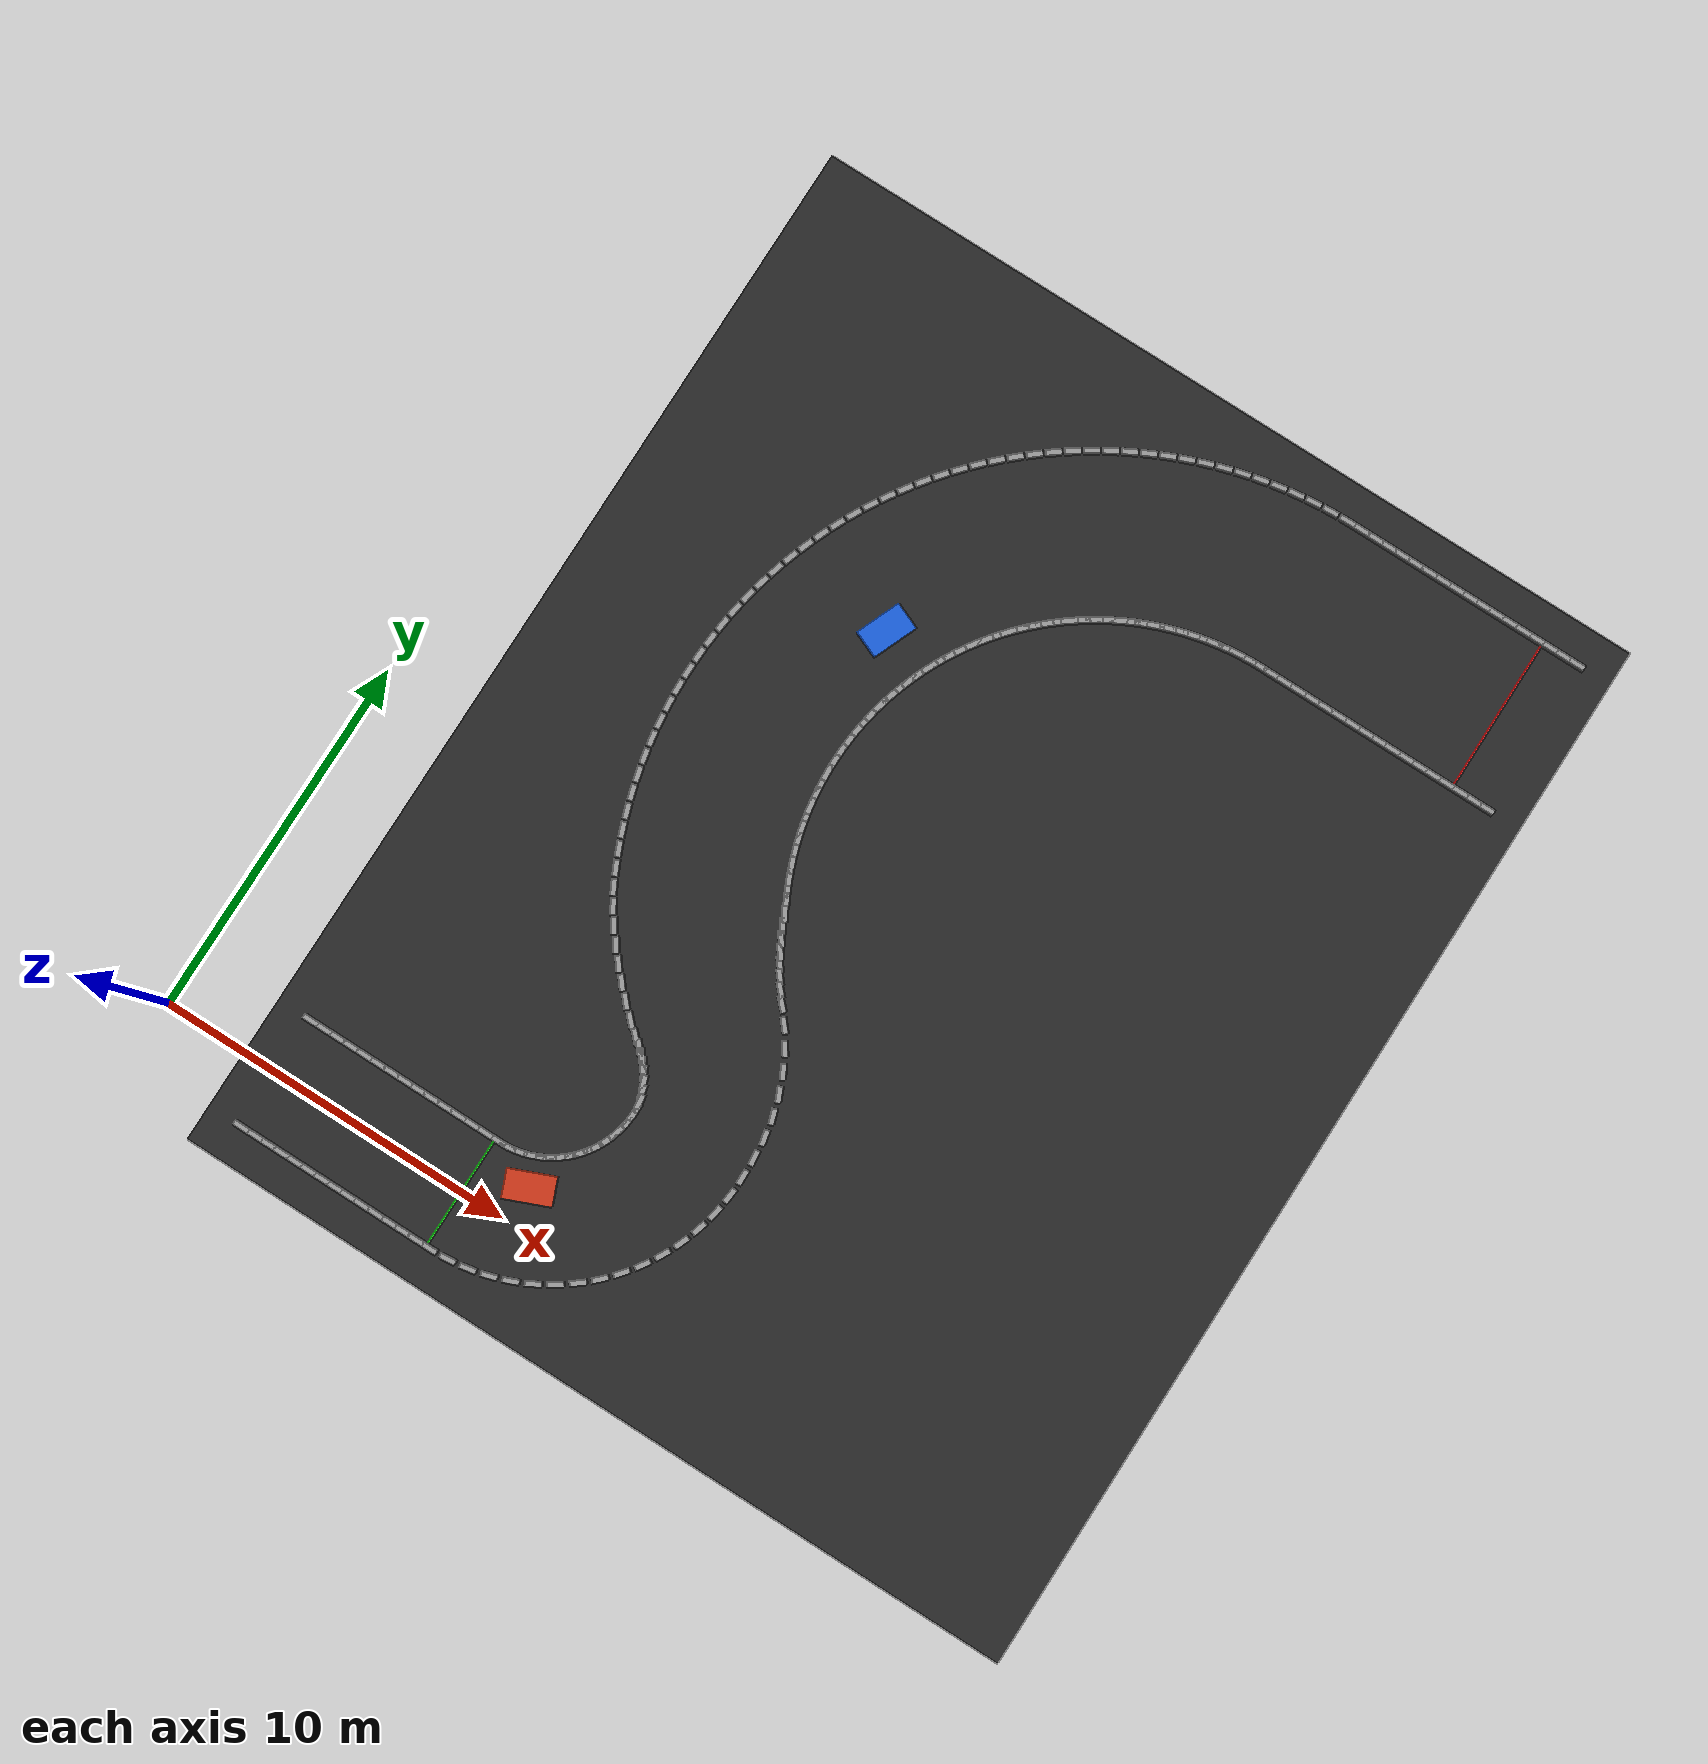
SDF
<?xml version="1.0"?>
<sdf version="1.10">
  <world name="s_curve_avoidance">
    <physics name="default_physics" type="ode">
      <max_step_size>0.001</max_step_size>
      <real_time_factor>1.0</real_time_factor>
    </physics>
    <plugin filename="gz-sim-physics-system" name="gz::sim::systems::Physics"/>
    <plugin filename="gz-sim-user-commands-system" name="gz::sim::systems::UserCommands"/>
    <plugin filename="gz-sim-scene-broadcaster-system" name="gz::sim::systems::SceneBroadcaster"/>
    <plugin filename="gz-sim-sensors-system" name="gz::sim::systems::Sensors">
      <render_engine>ogre2</render_engine>
    </plugin>
    <gravity>0 0 -9.81</gravity>
    <scene>
      <ambient>0.65 0.65 0.65 1</ambient>
      <background>0.78 0.85 0.92 1</background>
      <shadows>true</shadows>
    </scene>
    <light type="directional" name="sun">
      <cast_shadows>true</cast_shadows>
      <pose>20 10 22 0 0 0</pose>
      <diffuse>0.9 0.9 0.9 1</diffuse>
      <specular>0.2 0.2 0.2 1</specular>
      <direction>-0.4 0.1 -0.9</direction>
    </light>

    <model name="s_curve_course">
      <static>true</static>
      <link name="continuous_course">
        <collision name="road_collision">
          <pose>14.245784 12.356933 -0.050000 0 0 0</pose>
          <geometry><box><size>23.991569 29.863866 0.050000</size></box></geometry>
        </collision>
        <visual name="road_visual">
          <pose>14.245784 12.356933 -0.050000 0 0 0</pose>
          <geometry><box><size>23.991569 29.863866 0.050000</size></box></geometry>
          <material><ambient>0.14 0.14 0.14 1</ambient><diffuse>0.16 0.16 0.16 1</diffuse></material>
        </visual>
      </link>
    </model>

    <model name="left_curb_seg_0000">
      <static>true</static>
      <pose>3.250000 1.575000 0.090000 0 0 0.000000</pose>
      <link name="curb">
        <collision name="collision">
          <geometry><box><size>0.432000 0.150000 0.180000</size></box></geometry>
        </collision>
        <visual name="visual">
          <geometry><box><size>0.432000 0.150000 0.180000</size></box></geometry>
          <material><ambient>0.58 0.58 0.58 1</ambient><diffuse>0.62 0.62 0.62 1</diffuse></material>
        </visual>
      </link>
    </model>
    <model name="left_curb_seg_0001">
      <static>true</static>
      <pose>3.650000 1.575000 0.090000 0 0 0.000000</pose>
      <link name="curb">
        <collision name="collision">
          <geometry><box><size>0.432000 0.150000 0.180000</size></box></geometry>
        </collision>
        <visual name="visual">
          <geometry><box><size>0.432000 0.150000 0.180000</size></box></geometry>
          <material><ambient>0.58 0.58 0.58 1</ambient><diffuse>0.62 0.62 0.62 1</diffuse></material>
        </visual>
      </link>
    </model>
    <model name="left_curb_seg_0002">
      <static>true</static>
      <pose>4.050000 1.575000 0.090000 0 0 0.000000</pose>
      <link name="curb">
        <collision name="collision">
          <geometry><box><size>0.432000 0.150000 0.180000</size></box></geometry>
        </collision>
        <visual name="visual">
          <geometry><box><size>0.432000 0.150000 0.180000</size></box></geometry>
          <material><ambient>0.58 0.58 0.58 1</ambient><diffuse>0.62 0.62 0.62 1</diffuse></material>
        </visual>
      </link>
    </model>
    <model name="left_curb_seg_0003">
      <static>true</static>
      <pose>4.450000 1.575000 0.090000 0 0 0.000000</pose>
      <link name="curb">
        <collision name="collision">
          <geometry><box><size>0.432000 0.150000 0.180000</size></box></geometry>
        </collision>
        <visual name="visual">
          <geometry><box><size>0.432000 0.150000 0.180000</size></box></geometry>
          <material><ambient>0.58 0.58 0.58 1</ambient><diffuse>0.62 0.62 0.62 1</diffuse></material>
        </visual>
      </link>
    </model>
    <model name="left_curb_seg_0004">
      <static>true</static>
      <pose>4.850000 1.575000 0.090000 0 0 0.000000</pose>
      <link name="curb">
        <collision name="collision">
          <geometry><box><size>0.432000 0.150000 0.180000</size></box></geometry>
        </collision>
        <visual name="visual">
          <geometry><box><size>0.432000 0.150000 0.180000</size></box></geometry>
          <material><ambient>0.58 0.58 0.58 1</ambient><diffuse>0.62 0.62 0.62 1</diffuse></material>
        </visual>
      </link>
    </model>
    <model name="left_curb_seg_0005">
      <static>true</static>
      <pose>5.250000 1.575000 0.090000 0 0 0.000000</pose>
      <link name="curb">
        <collision name="collision">
          <geometry><box><size>0.432000 0.150000 0.180000</size></box></geometry>
        </collision>
        <visual name="visual">
          <geometry><box><size>0.432000 0.150000 0.180000</size></box></geometry>
          <material><ambient>0.58 0.58 0.58 1</ambient><diffuse>0.62 0.62 0.62 1</diffuse></material>
        </visual>
      </link>
    </model>
    <model name="left_curb_seg_0006">
      <static>true</static>
      <pose>5.650000 1.575000 0.090000 0 0 0.000000</pose>
      <link name="curb">
        <collision name="collision">
          <geometry><box><size>0.432000 0.150000 0.180000</size></box></geometry>
        </collision>
        <visual name="visual">
          <geometry><box><size>0.432000 0.150000 0.180000</size></box></geometry>
          <material><ambient>0.58 0.58 0.58 1</ambient><diffuse>0.62 0.62 0.62 1</diffuse></material>
        </visual>
      </link>
    </model>
    <model name="left_curb_seg_0007">
      <static>true</static>
      <pose>6.050000 1.575000 0.090000 0 0 0.000000</pose>
      <link name="curb">
        <collision name="collision">
          <geometry><box><size>0.432000 0.150000 0.180000</size></box></geometry>
        </collision>
        <visual name="visual">
          <geometry><box><size>0.432000 0.150000 0.180000</size></box></geometry>
          <material><ambient>0.58 0.58 0.58 1</ambient><diffuse>0.62 0.62 0.62 1</diffuse></material>
        </visual>
      </link>
    </model>
    <model name="left_curb_seg_0008">
      <static>true</static>
      <pose>6.450000 1.575000 0.090000 0 0 0.000000</pose>
      <link name="curb">
        <collision name="collision">
          <geometry><box><size>0.432000 0.150000 0.180000</size></box></geometry>
        </collision>
        <visual name="visual">
          <geometry><box><size>0.432000 0.150000 0.180000</size></box></geometry>
          <material><ambient>0.58 0.58 0.58 1</ambient><diffuse>0.62 0.62 0.62 1</diffuse></material>
        </visual>
      </link>
    </model>
    <model name="left_curb_seg_0009">
      <static>true</static>
      <pose>6.850000 1.575000 0.090000 0 0 0.000000</pose>
      <link name="curb">
        <collision name="collision">
          <geometry><box><size>0.432000 0.150000 0.180000</size></box></geometry>
        </collision>
        <visual name="visual">
          <geometry><box><size>0.432000 0.150000 0.180000</size></box></geometry>
          <material><ambient>0.58 0.58 0.58 1</ambient><diffuse>0.62 0.62 0.62 1</diffuse></material>
        </visual>
      </link>
    </model>
    <model name="left_curb_seg_0010">
      <static>true</static>
      <pose>7.250000 1.575000 0.090000 0 0 0.000000</pose>
      <link name="curb">
        <collision name="collision">
          <geometry><box><size>0.432000 0.150000 0.180000</size></box></geometry>
        </collision>
        <visual name="visual">
          <geometry><box><size>0.432000 0.150000 0.180000</size></box></geometry>
          <material><ambient>0.58 0.58 0.58 1</ambient><diffuse>0.62 0.62 0.62 1</diffuse></material>
        </visual>
      </link>
    </model>
    <model name="left_curb_seg_0011">
      <static>true</static>
      <pose>7.650000 1.575000 0.090000 0 0 0.000000</pose>
      <link name="curb">
        <collision name="collision">
          <geometry><box><size>0.432000 0.150000 0.180000</size></box></geometry>
        </collision>
        <visual name="visual">
          <geometry><box><size>0.432000 0.150000 0.180000</size></box></geometry>
          <material><ambient>0.58 0.58 0.58 1</ambient><diffuse>0.62 0.62 0.62 1</diffuse></material>
        </visual>
      </link>
    </model>
    <model name="left_curb_seg_0012">
      <static>true</static>
      <pose>8.050000 1.575000 0.090000 0 0 0.000000</pose>
      <link name="curb">
        <collision name="collision">
          <geometry><box><size>0.432000 0.150000 0.180000</size></box></geometry>
        </collision>
        <visual name="visual">
          <geometry><box><size>0.432000 0.150000 0.180000</size></box></geometry>
          <material><ambient>0.58 0.58 0.58 1</ambient><diffuse>0.62 0.62 0.62 1</diffuse></material>
        </visual>
      </link>
    </model>
    <model name="left_curb_seg_0013">
      <static>true</static>
      <pose>8.450000 1.575000 0.090000 0 0 0.000000</pose>
      <link name="curb">
        <collision name="collision">
          <geometry><box><size>0.432000 0.150000 0.180000</size></box></geometry>
        </collision>
        <visual name="visual">
          <geometry><box><size>0.432000 0.150000 0.180000</size></box></geometry>
          <material><ambient>0.58 0.58 0.58 1</ambient><diffuse>0.62 0.62 0.62 1</diffuse></material>
        </visual>
      </link>
    </model>
    <model name="left_curb_seg_0014">
      <static>true</static>
      <pose>8.843437 1.575126 0.090000 0 0 0.004167</pose>
      <link name="curb">
        <collision name="collision">
          <geometry><box><size>0.432000 0.150000 0.180000</size></box></geometry>
        </collision>
        <visual name="visual">
          <geometry><box><size>0.432000 0.150000 0.180000</size></box></geometry>
          <material><ambient>0.58 0.58 0.58 1</ambient><diffuse>0.62 0.62 0.62 1</diffuse></material>
        </visual>
      </link>
    </model>
    <model name="left_curb_seg_0015">
      <static>true</static>
      <pose>9.111910 1.585217 0.090000 0 0 0.087500</pose>
      <link name="curb">
        <collision name="collision">
          <geometry><box><size>0.432000 0.150000 0.180000</size></box></geometry>
        </collision>
        <visual name="visual">
          <geometry><box><size>0.432000 0.150000 0.180000</size></box></geometry>
          <material><ambient>0.58 0.58 0.58 1</ambient><diffuse>0.62 0.62 0.62 1</diffuse></material>
        </visual>
      </link>
    </model>
    <model name="left_curb_seg_0016">
      <static>true</static>
      <pose>9.352021 1.618442 0.090000 0 0 0.187500</pose>
      <link name="curb">
        <collision name="collision">
          <geometry><box><size>0.432000 0.150000 0.180000</size></box></geometry>
        </collision>
        <visual name="visual">
          <geometry><box><size>0.432000 0.150000 0.180000</size></box></geometry>
          <material><ambient>0.58 0.58 0.58 1</ambient><diffuse>0.62 0.62 0.62 1</diffuse></material>
        </visual>
      </link>
    </model>
    <model name="left_curb_seg_0017">
      <static>true</static>
      <pose>9.587615 1.675472 0.090000 0 0 0.287500</pose>
      <link name="curb">
        <collision name="collision">
          <geometry><box><size>0.432000 0.150000 0.180000</size></box></geometry>
        </collision>
        <visual name="visual">
          <geometry><box><size>0.432000 0.150000 0.180000</size></box></geometry>
          <material><ambient>0.58 0.58 0.58 1</ambient><diffuse>0.62 0.62 0.62 1</diffuse></material>
        </visual>
      </link>
    </model>
    <model name="left_curb_seg_0018">
      <static>true</static>
      <pose>9.816339 1.755737 0.090000 0 0 0.387500</pose>
      <link name="curb">
        <collision name="collision">
          <geometry><box><size>0.432000 0.150000 0.180000</size></box></geometry>
        </collision>
        <visual name="visual">
          <geometry><box><size>0.432000 0.150000 0.180000</size></box></geometry>
          <material><ambient>0.58 0.58 0.58 1</ambient><diffuse>0.62 0.62 0.62 1</diffuse></material>
        </visual>
      </link>
    </model>
    <model name="left_curb_seg_0019">
      <static>true</static>
      <pose>10.035907 1.858436 0.090000 0 0 0.487500</pose>
      <link name="curb">
        <collision name="collision">
          <geometry><box><size>0.432000 0.150000 0.180000</size></box></geometry>
        </collision>
        <visual name="visual">
          <geometry><box><size>0.432000 0.150000 0.180000</size></box></geometry>
          <material><ambient>0.58 0.58 0.58 1</ambient><diffuse>0.62 0.62 0.62 1</diffuse></material>
        </visual>
      </link>
    </model>
    <model name="left_curb_seg_0020">
      <static>true</static>
      <pose>10.244126 1.982541 0.090000 0 0 0.587500</pose>
      <link name="curb">
        <collision name="collision">
          <geometry><box><size>0.432000 0.150000 0.180000</size></box></geometry>
        </collision>
        <visual name="visual">
          <geometry><box><size>0.432000 0.150000 0.180000</size></box></geometry>
          <material><ambient>0.58 0.58 0.58 1</ambient><diffuse>0.62 0.62 0.62 1</diffuse></material>
        </visual>
      </link>
    </model>
    <model name="left_curb_seg_0021">
      <static>true</static>
      <pose>10.438914 2.126814 0.090000 0 0 0.687500</pose>
      <link name="curb">
        <collision name="collision">
          <geometry><box><size>0.432000 0.150000 0.180000</size></box></geometry>
        </collision>
        <visual name="visual">
          <geometry><box><size>0.432000 0.150000 0.180000</size></box></geometry>
          <material><ambient>0.58 0.58 0.58 1</ambient><diffuse>0.62 0.62 0.62 1</diffuse></material>
        </visual>
      </link>
    </model>
    <model name="left_curb_seg_0022">
      <static>true</static>
      <pose>10.618326 2.289813 0.090000 0 0 0.787500</pose>
      <link name="curb">
        <collision name="collision">
          <geometry><box><size>0.432000 0.150000 0.180000</size></box></geometry>
        </collision>
        <visual name="visual">
          <geometry><box><size>0.432000 0.150000 0.180000</size></box></geometry>
          <material><ambient>0.58 0.58 0.58 1</ambient><diffuse>0.62 0.62 0.62 1</diffuse></material>
        </visual>
      </link>
    </model>
    <model name="left_curb_seg_0023">
      <static>true</static>
      <pose>10.780569 2.469908 0.090000 0 0 0.887500</pose>
      <link name="curb">
        <collision name="collision">
          <geometry><box><size>0.432000 0.150000 0.180000</size></box></geometry>
        </collision>
        <visual name="visual">
          <geometry><box><size>0.432000 0.150000 0.180000</size></box></geometry>
          <material><ambient>0.58 0.58 0.58 1</ambient><diffuse>0.62 0.62 0.62 1</diffuse></material>
        </visual>
      </link>
    </model>
    <model name="left_curb_seg_0024">
      <static>true</static>
      <pose>10.924021 2.665301 0.090000 0 0 0.987500</pose>
      <link name="curb">
        <collision name="collision">
          <geometry><box><size>0.432000 0.150000 0.180000</size></box></geometry>
        </collision>
        <visual name="visual">
          <geometry><box><size>0.432000 0.150000 0.180000</size></box></geometry>
          <material><ambient>0.58 0.58 0.58 1</ambient><diffuse>0.62 0.62 0.62 1</diffuse></material>
        </visual>
      </link>
    </model>
    <model name="left_curb_seg_0025">
      <static>true</static>
      <pose>11.047251 2.874040 0.090000 0 0 1.087500</pose>
      <link name="curb">
        <collision name="collision">
          <geometry><box><size>0.432000 0.150000 0.180000</size></box></geometry>
        </collision>
        <visual name="visual">
          <geometry><box><size>0.432000 0.150000 0.180000</size></box></geometry>
          <material><ambient>0.58 0.58 0.58 1</ambient><diffuse>0.62 0.62 0.62 1</diffuse></material>
        </visual>
      </link>
    </model>
    <model name="left_curb_seg_0026">
      <static>true</static>
      <pose>11.149026 3.094038 0.090000 0 0 1.187500</pose>
      <link name="curb">
        <collision name="collision">
          <geometry><box><size>0.432000 0.150000 0.180000</size></box></geometry>
        </collision>
        <visual name="visual">
          <geometry><box><size>0.432000 0.150000 0.180000</size></box></geometry>
          <material><ambient>0.58 0.58 0.58 1</ambient><diffuse>0.62 0.62 0.62 1</diffuse></material>
        </visual>
      </link>
    </model>
    <model name="left_curb_seg_0027">
      <static>true</static>
      <pose>11.228329 3.323097 0.090000 0 0 1.287500</pose>
      <link name="curb">
        <collision name="collision">
          <geometry><box><size>0.432000 0.150000 0.180000</size></box></geometry>
        </collision>
        <visual name="visual">
          <geometry><box><size>0.432000 0.150000 0.180000</size></box></geometry>
          <material><ambient>0.58 0.58 0.58 1</ambient><diffuse>0.62 0.62 0.62 1</diffuse></material>
        </visual>
      </link>
    </model>
    <model name="left_curb_seg_0028">
      <static>true</static>
      <pose>11.284368 3.558929 0.090000 0 0 1.387500</pose>
      <link name="curb">
        <collision name="collision">
          <geometry><box><size>0.432000 0.150000 0.180000</size></box></geometry>
        </collision>
        <visual name="visual">
          <geometry><box><size>0.432000 0.150000 0.180000</size></box></geometry>
          <material><ambient>0.58 0.58 0.58 1</ambient><diffuse>0.62 0.62 0.62 1</diffuse></material>
        </visual>
      </link>
    </model>
    <model name="left_curb_seg_0029">
      <static>true</static>
      <pose>11.316583 3.799178 0.090000 0 0 1.487500</pose>
      <link name="curb">
        <collision name="collision">
          <geometry><box><size>0.432000 0.150000 0.180000</size></box></geometry>
        </collision>
        <visual name="visual">
          <geometry><box><size>0.432000 0.150000 0.180000</size></box></geometry>
          <material><ambient>0.58 0.58 0.58 1</ambient><diffuse>0.62 0.62 0.62 1</diffuse></material>
        </visual>
      </link>
    </model>
    <model name="left_curb_seg_0030">
      <static>true</static>
      <pose>11.324653 4.041442 0.090000 0 0 1.587500</pose>
      <link name="curb">
        <collision name="collision">
          <geometry><box><size>0.432000 0.150000 0.180000</size></box></geometry>
        </collision>
        <visual name="visual">
          <geometry><box><size>0.432000 0.150000 0.180000</size></box></geometry>
          <material><ambient>0.58 0.58 0.58 1</ambient><diffuse>0.62 0.62 0.62 1</diffuse></material>
        </visual>
      </link>
    </model>
    <model name="left_curb_seg_0031">
      <static>true</static>
      <pose>11.291093 4.281261 0.090000 0 0 1.687500</pose>
      <link name="curb">
        <collision name="collision">
          <geometry><box><size>0.432000 0.150000 0.180000</size></box></geometry>
        </collision>
        <visual name="visual">
          <geometry><box><size>0.432000 0.150000 0.180000</size></box></geometry>
          <material><ambient>0.58 0.58 0.58 1</ambient><diffuse>0.62 0.62 0.62 1</diffuse></material>
        </visual>
      </link>
    </model>
    <model name="left_curb_seg_0032">
      <static>true</static>
      <pose>11.212097 4.509972 0.090000 0 0 1.787500</pose>
      <link name="curb">
        <collision name="collision">
          <geometry><box><size>0.432000 0.150000 0.180000</size></box></geometry>
        </collision>
        <visual name="visual">
          <geometry><box><size>0.432000 0.150000 0.180000</size></box></geometry>
          <material><ambient>0.58 0.58 0.58 1</ambient><diffuse>0.62 0.62 0.62 1</diffuse></material>
        </visual>
      </link>
    </model>
    <model name="left_curb_seg_0033">
      <static>true</static>
      <pose>11.111717 4.725797 0.090000 0 0 1.887500</pose>
      <link name="curb">
        <collision name="collision">
          <geometry><box><size>0.432000 0.150000 0.180000</size></box></geometry>
        </collision>
        <visual name="visual">
          <geometry><box><size>0.432000 0.150000 0.180000</size></box></geometry>
          <material><ambient>0.58 0.58 0.58 1</ambient><diffuse>0.62 0.62 0.62 1</diffuse></material>
        </visual>
      </link>
    </model>
    <model name="left_curb_seg_0034">
      <static>true</static>
      <pose>10.991725 4.926790 0.090000 0 0 1.987500</pose>
      <link name="curb">
        <collision name="collision">
          <geometry><box><size>0.432000 0.150000 0.180000</size></box></geometry>
        </collision>
        <visual name="visual">
          <geometry><box><size>0.432000 0.150000 0.180000</size></box></geometry>
          <material><ambient>0.58 0.58 0.58 1</ambient><diffuse>0.62 0.62 0.62 1</diffuse></material>
        </visual>
      </link>
    </model>
    <model name="left_curb_seg_0035">
      <static>true</static>
      <pose>10.854066 5.111228 0.090000 0 0 2.087500</pose>
      <link name="curb">
        <collision name="collision">
          <geometry><box><size>0.432000 0.150000 0.180000</size></box></geometry>
        </collision>
        <visual name="visual">
          <geometry><box><size>0.432000 0.150000 0.180000</size></box></geometry>
          <material><ambient>0.58 0.58 0.58 1</ambient><diffuse>0.62 0.62 0.62 1</diffuse></material>
        </visual>
      </link>
    </model>
    <model name="left_curb_seg_0036">
      <static>true</static>
      <pose>10.700828 5.277629 0.090000 0 0 2.187500</pose>
      <link name="curb">
        <collision name="collision">
          <geometry><box><size>0.432000 0.150000 0.180000</size></box></geometry>
        </collision>
        <visual name="visual">
          <geometry><box><size>0.432000 0.150000 0.180000</size></box></geometry>
          <material><ambient>0.58 0.58 0.58 1</ambient><diffuse>0.62 0.62 0.62 1</diffuse></material>
        </visual>
      </link>
    </model>
    <model name="left_curb_seg_0037">
      <static>true</static>
      <pose>10.534216 5.424759 0.090000 0 0 2.287500</pose>
      <link name="curb">
        <collision name="collision">
          <geometry><box><size>0.432000 0.150000 0.180000</size></box></geometry>
        </collision>
        <visual name="visual">
          <geometry><box><size>0.432000 0.150000 0.180000</size></box></geometry>
          <material><ambient>0.58 0.58 0.58 1</ambient><diffuse>0.62 0.62 0.62 1</diffuse></material>
        </visual>
      </link>
    </model>
    <model name="left_curb_seg_0038">
      <static>true</static>
      <pose>10.316117 5.594848 0.090000 0 0 2.355928</pose>
      <link name="curb">
        <collision name="collision">
          <geometry><box><size>0.432000 0.150000 0.180000</size></box></geometry>
        </collision>
        <visual name="visual">
          <geometry><box><size>0.432000 0.150000 0.180000</size></box></geometry>
          <material><ambient>0.58 0.58 0.58 1</ambient><diffuse>0.62 0.62 0.62 1</diffuse></material>
        </visual>
      </link>
    </model>
    <model name="left_curb_seg_0039">
      <static>true</static>
      <pose>9.977306 5.881899 0.090000 0 0 2.333672</pose>
      <link name="curb">
        <collision name="collision">
          <geometry><box><size>0.432000 0.150000 0.180000</size></box></geometry>
        </collision>
        <visual name="visual">
          <geometry><box><size>0.432000 0.150000 0.180000</size></box></geometry>
          <material><ambient>0.58 0.58 0.58 1</ambient><diffuse>0.62 0.62 0.62 1</diffuse></material>
        </visual>
      </link>
    </model>
    <model name="left_curb_seg_0040">
      <static>true</static>
      <pose>9.625022 6.206370 0.090000 0 0 2.293672</pose>
      <link name="curb">
        <collision name="collision">
          <geometry><box><size>0.432000 0.150000 0.180000</size></box></geometry>
        </collision>
        <visual name="visual">
          <geometry><box><size>0.432000 0.150000 0.180000</size></box></geometry>
          <material><ambient>0.58 0.58 0.58 1</ambient><diffuse>0.62 0.62 0.62 1</diffuse></material>
        </visual>
      </link>
    </model>
    <model name="left_curb_seg_0041">
      <static>true</static>
      <pose>9.284961 6.545889 0.090000 0 0 2.253672</pose>
      <link name="curb">
        <collision name="collision">
          <geometry><box><size>0.432000 0.150000 0.180000</size></box></geometry>
        </collision>
        <visual name="visual">
          <geometry><box><size>0.432000 0.150000 0.180000</size></box></geometry>
          <material><ambient>0.58 0.58 0.58 1</ambient><diffuse>0.62 0.62 0.62 1</diffuse></material>
        </visual>
      </link>
    </model>
    <model name="left_curb_seg_0042">
      <static>true</static>
      <pose>8.957764 6.899996 0.090000 0 0 2.213672</pose>
      <link name="curb">
        <collision name="collision">
          <geometry><box><size>0.432000 0.150000 0.180000</size></box></geometry>
        </collision>
        <visual name="visual">
          <geometry><box><size>0.432000 0.150000 0.180000</size></box></geometry>
          <material><ambient>0.58 0.58 0.58 1</ambient><diffuse>0.62 0.62 0.62 1</diffuse></material>
        </visual>
      </link>
    </model>
    <model name="left_curb_seg_0043">
      <static>true</static>
      <pose>8.644057 7.268204 0.090000 0 0 2.173672</pose>
      <link name="curb">
        <collision name="collision">
          <geometry><box><size>0.432000 0.150000 0.180000</size></box></geometry>
        </collision>
        <visual name="visual">
          <geometry><box><size>0.432000 0.150000 0.180000</size></box></geometry>
          <material><ambient>0.58 0.58 0.58 1</ambient><diffuse>0.62 0.62 0.62 1</diffuse></material>
        </visual>
      </link>
    </model>
    <model name="left_curb_seg_0044">
      <static>true</static>
      <pose>8.344444 7.649998 0.090000 0 0 2.133672</pose>
      <link name="curb">
        <collision name="collision">
          <geometry><box><size>0.432000 0.150000 0.180000</size></box></geometry>
        </collision>
        <visual name="visual">
          <geometry><box><size>0.432000 0.150000 0.180000</size></box></geometry>
          <material><ambient>0.58 0.58 0.58 1</ambient><diffuse>0.62 0.62 0.62 1</diffuse></material>
        </visual>
      </link>
    </model>
    <model name="left_curb_seg_0045">
      <static>true</static>
      <pose>8.059511 8.044838 0.090000 0 0 2.093672</pose>
      <link name="curb">
        <collision name="collision">
          <geometry><box><size>0.432000 0.150000 0.180000</size></box></geometry>
        </collision>
        <visual name="visual">
          <geometry><box><size>0.432000 0.150000 0.180000</size></box></geometry>
          <material><ambient>0.58 0.58 0.58 1</ambient><diffuse>0.62 0.62 0.62 1</diffuse></material>
        </visual>
      </link>
    </model>
    <model name="left_curb_seg_0046">
      <static>true</static>
      <pose>7.805344 8.460294 0.090000 0 0 2.053672</pose>
      <link name="curb">
        <collision name="collision">
          <geometry><box><size>0.432000 0.150000 0.180000</size></box></geometry>
        </collision>
        <visual name="visual">
          <geometry><box><size>0.432000 0.150000 0.180000</size></box></geometry>
          <material><ambient>0.58 0.58 0.58 1</ambient><diffuse>0.62 0.62 0.62 1</diffuse></material>
        </visual>
      </link>
    </model>
    <model name="left_curb_seg_0047">
      <static>true</static>
      <pose>7.587902 8.896019 0.090000 0 0 2.013672</pose>
      <link name="curb">
        <collision name="collision">
          <geometry><box><size>0.432000 0.150000 0.180000</size></box></geometry>
        </collision>
        <visual name="visual">
          <geometry><box><size>0.432000 0.150000 0.180000</size></box></geometry>
          <material><ambient>0.58 0.58 0.58 1</ambient><diffuse>0.62 0.62 0.62 1</diffuse></material>
        </visual>
      </link>
    </model>
    <model name="left_curb_seg_0048">
      <static>true</static>
      <pose>7.388058 9.340091 0.090000 0 0 1.973672</pose>
      <link name="curb">
        <collision name="collision">
          <geometry><box><size>0.432000 0.150000 0.180000</size></box></geometry>
        </collision>
        <visual name="visual">
          <geometry><box><size>0.432000 0.150000 0.180000</size></box></geometry>
          <material><ambient>0.58 0.58 0.58 1</ambient><diffuse>0.62 0.62 0.62 1</diffuse></material>
        </visual>
      </link>
    </model>
    <model name="left_curb_seg_0049">
      <static>true</static>
      <pose>7.206132 9.791799 0.090000 0 0 1.933672</pose>
      <link name="curb">
        <collision name="collision">
          <geometry><box><size>0.432000 0.150000 0.180000</size></box></geometry>
        </collision>
        <visual name="visual">
          <geometry><box><size>0.432000 0.150000 0.180000</size></box></geometry>
          <material><ambient>0.58 0.58 0.58 1</ambient><diffuse>0.62 0.62 0.62 1</diffuse></material>
        </visual>
      </link>
    </model>
    <model name="left_curb_seg_0050">
      <static>true</static>
      <pose>7.042415 10.250421 0.090000 0 0 1.893672</pose>
      <link name="curb">
        <collision name="collision">
          <geometry><box><size>0.432000 0.150000 0.180000</size></box></geometry>
        </collision>
        <visual name="visual">
          <geometry><box><size>0.432000 0.150000 0.180000</size></box></geometry>
          <material><ambient>0.58 0.58 0.58 1</ambient><diffuse>0.62 0.62 0.62 1</diffuse></material>
        </visual>
      </link>
    </model>
    <model name="left_curb_seg_0051">
      <static>true</static>
      <pose>6.897169 10.715223 0.090000 0 0 1.853672</pose>
      <link name="curb">
        <collision name="collision">
          <geometry><box><size>0.432000 0.150000 0.180000</size></box></geometry>
        </collision>
        <visual name="visual">
          <geometry><box><size>0.432000 0.150000 0.180000</size></box></geometry>
          <material><ambient>0.58 0.58 0.58 1</ambient><diffuse>0.62 0.62 0.62 1</diffuse></material>
        </visual>
      </link>
    </model>
    <model name="left_curb_seg_0052">
      <static>true</static>
      <pose>6.770626 11.185461 0.090000 0 0 1.813672</pose>
      <link name="curb">
        <collision name="collision">
          <geometry><box><size>0.432000 0.150000 0.180000</size></box></geometry>
        </collision>
        <visual name="visual">
          <geometry><box><size>0.432000 0.150000 0.180000</size></box></geometry>
          <material><ambient>0.58 0.58 0.58 1</ambient><diffuse>0.62 0.62 0.62 1</diffuse></material>
        </visual>
      </link>
    </model>
    <model name="left_curb_seg_0053">
      <static>true</static>
      <pose>6.662989 11.660384 0.090000 0 0 1.773672</pose>
      <link name="curb">
        <collision name="collision">
          <geometry><box><size>0.432000 0.150000 0.180000</size></box></geometry>
        </collision>
        <visual name="visual">
          <geometry><box><size>0.432000 0.150000 0.180000</size></box></geometry>
          <material><ambient>0.58 0.58 0.58 1</ambient><diffuse>0.62 0.62 0.62 1</diffuse></material>
        </visual>
      </link>
    </model>
    <model name="left_curb_seg_0054">
      <static>true</static>
      <pose>6.574430 12.139231 0.090000 0 0 1.733672</pose>
      <link name="curb">
        <collision name="collision">
          <geometry><box><size>0.432000 0.150000 0.180000</size></box></geometry>
        </collision>
        <visual name="visual">
          <geometry><box><size>0.432000 0.150000 0.180000</size></box></geometry>
          <material><ambient>0.58 0.58 0.58 1</ambient><diffuse>0.62 0.62 0.62 1</diffuse></material>
        </visual>
      </link>
    </model>
    <model name="left_curb_seg_0055">
      <static>true</static>
      <pose>6.505090 12.621237 0.090000 0 0 1.693672</pose>
      <link name="curb">
        <collision name="collision">
          <geometry><box><size>0.432000 0.150000 0.180000</size></box></geometry>
        </collision>
        <visual name="visual">
          <geometry><box><size>0.432000 0.150000 0.180000</size></box></geometry>
          <material><ambient>0.58 0.58 0.58 1</ambient><diffuse>0.62 0.62 0.62 1</diffuse></material>
        </visual>
      </link>
    </model>
    <model name="left_curb_seg_0056">
      <static>true</static>
      <pose>6.455081 13.105630 0.090000 0 0 1.653672</pose>
      <link name="curb">
        <collision name="collision">
          <geometry><box><size>0.432000 0.150000 0.180000</size></box></geometry>
        </collision>
        <visual name="visual">
          <geometry><box><size>0.432000 0.150000 0.180000</size></box></geometry>
          <material><ambient>0.58 0.58 0.58 1</ambient><diffuse>0.62 0.62 0.62 1</diffuse></material>
        </visual>
      </link>
    </model>
    <model name="left_curb_seg_0057">
      <static>true</static>
      <pose>6.424483 13.591635 0.090000 0 0 1.613672</pose>
      <link name="curb">
        <collision name="collision">
          <geometry><box><size>0.432000 0.150000 0.180000</size></box></geometry>
        </collision>
        <visual name="visual">
          <geometry><box><size>0.432000 0.150000 0.180000</size></box></geometry>
          <material><ambient>0.58 0.58 0.58 1</ambient><diffuse>0.62 0.62 0.62 1</diffuse></material>
        </visual>
      </link>
    </model>
    <model name="left_curb_seg_0058">
      <static>true</static>
      <pose>6.413344 14.078475 0.090000 0 0 1.573672</pose>
      <link name="curb">
        <collision name="collision">
          <geometry><box><size>0.432000 0.150000 0.180000</size></box></geometry>
        </collision>
        <visual name="visual">
          <geometry><box><size>0.432000 0.150000 0.180000</size></box></geometry>
          <material><ambient>0.58 0.58 0.58 1</ambient><diffuse>0.62 0.62 0.62 1</diffuse></material>
        </visual>
      </link>
    </model>
    <model name="left_curb_seg_0059">
      <static>true</static>
      <pose>6.421682 14.565371 0.090000 0 0 1.533672</pose>
      <link name="curb">
        <collision name="collision">
          <geometry><box><size>0.432000 0.150000 0.180000</size></box></geometry>
        </collision>
        <visual name="visual">
          <geometry><box><size>0.432000 0.150000 0.180000</size></box></geometry>
          <material><ambient>0.58 0.58 0.58 1</ambient><diffuse>0.62 0.62 0.62 1</diffuse></material>
        </visual>
      </link>
    </model>
    <model name="left_curb_seg_0060">
      <static>true</static>
      <pose>6.449485 15.051544 0.090000 0 0 1.493672</pose>
      <link name="curb">
        <collision name="collision">
          <geometry><box><size>0.432000 0.150000 0.180000</size></box></geometry>
        </collision>
        <visual name="visual">
          <geometry><box><size>0.432000 0.150000 0.180000</size></box></geometry>
          <material><ambient>0.58 0.58 0.58 1</ambient><diffuse>0.62 0.62 0.62 1</diffuse></material>
        </visual>
      </link>
    </model>
    <model name="left_curb_seg_0061">
      <static>true</static>
      <pose>6.496707 15.536217 0.090000 0 0 1.453672</pose>
      <link name="curb">
        <collision name="collision">
          <geometry><box><size>0.432000 0.150000 0.180000</size></box></geometry>
        </collision>
        <visual name="visual">
          <geometry><box><size>0.432000 0.150000 0.180000</size></box></geometry>
          <material><ambient>0.58 0.58 0.58 1</ambient><diffuse>0.62 0.62 0.62 1</diffuse></material>
        </visual>
      </link>
    </model>
    <model name="left_curb_seg_0062">
      <static>true</static>
      <pose>6.563273 16.018613 0.090000 0 0 1.413672</pose>
      <link name="curb">
        <collision name="collision">
          <geometry><box><size>0.432000 0.150000 0.180000</size></box></geometry>
        </collision>
        <visual name="visual">
          <geometry><box><size>0.432000 0.150000 0.180000</size></box></geometry>
          <material><ambient>0.58 0.58 0.58 1</ambient><diffuse>0.62 0.62 0.62 1</diffuse></material>
        </visual>
      </link>
    </model>
    <model name="left_curb_seg_0063">
      <static>true</static>
      <pose>6.649076 16.497962 0.090000 0 0 1.373672</pose>
      <link name="curb">
        <collision name="collision">
          <geometry><box><size>0.432000 0.150000 0.180000</size></box></geometry>
        </collision>
        <visual name="visual">
          <geometry><box><size>0.432000 0.150000 0.180000</size></box></geometry>
          <material><ambient>0.58 0.58 0.58 1</ambient><diffuse>0.62 0.62 0.62 1</diffuse></material>
        </visual>
      </link>
    </model>
    <model name="left_curb_seg_0064">
      <static>true</static>
      <pose>6.753980 16.973496 0.090000 0 0 1.333672</pose>
      <link name="curb">
        <collision name="collision">
          <geometry><box><size>0.432000 0.150000 0.180000</size></box></geometry>
        </collision>
        <visual name="visual">
          <geometry><box><size>0.432000 0.150000 0.180000</size></box></geometry>
          <material><ambient>0.58 0.58 0.58 1</ambient><diffuse>0.62 0.62 0.62 1</diffuse></material>
        </visual>
      </link>
    </model>
    <model name="left_curb_seg_0065">
      <static>true</static>
      <pose>6.877816 17.444455 0.090000 0 0 1.293672</pose>
      <link name="curb">
        <collision name="collision">
          <geometry><box><size>0.432000 0.150000 0.180000</size></box></geometry>
        </collision>
        <visual name="visual">
          <geometry><box><size>0.432000 0.150000 0.180000</size></box></geometry>
          <material><ambient>0.58 0.58 0.58 1</ambient><diffuse>0.62 0.62 0.62 1</diffuse></material>
        </visual>
      </link>
    </model>
    <model name="left_curb_seg_0066">
      <static>true</static>
      <pose>7.020386 17.910084 0.090000 0 0 1.253672</pose>
      <link name="curb">
        <collision name="collision">
          <geometry><box><size>0.432000 0.150000 0.180000</size></box></geometry>
        </collision>
        <visual name="visual">
          <geometry><box><size>0.432000 0.150000 0.180000</size></box></geometry>
          <material><ambient>0.58 0.58 0.58 1</ambient><diffuse>0.62 0.62 0.62 1</diffuse></material>
        </visual>
      </link>
    </model>
    <model name="left_curb_seg_0067">
      <static>true</static>
      <pose>7.181462 18.369640 0.090000 0 0 1.213672</pose>
      <link name="curb">
        <collision name="collision">
          <geometry><box><size>0.432000 0.150000 0.180000</size></box></geometry>
        </collision>
        <visual name="visual">
          <geometry><box><size>0.432000 0.150000 0.180000</size></box></geometry>
          <material><ambient>0.58 0.58 0.58 1</ambient><diffuse>0.62 0.62 0.62 1</diffuse></material>
        </visual>
      </link>
    </model>
    <model name="left_curb_seg_0068">
      <static>true</static>
      <pose>7.360787 18.822387 0.090000 0 0 1.173672</pose>
      <link name="curb">
        <collision name="collision">
          <geometry><box><size>0.432000 0.150000 0.180000</size></box></geometry>
        </collision>
        <visual name="visual">
          <geometry><box><size>0.432000 0.150000 0.180000</size></box></geometry>
          <material><ambient>0.58 0.58 0.58 1</ambient><diffuse>0.62 0.62 0.62 1</diffuse></material>
        </visual>
      </link>
    </model>
    <model name="left_curb_seg_0069">
      <static>true</static>
      <pose>7.558073 19.267601 0.090000 0 0 1.133672</pose>
      <link name="curb">
        <collision name="collision">
          <geometry><box><size>0.432000 0.150000 0.180000</size></box></geometry>
        </collision>
        <visual name="visual">
          <geometry><box><size>0.432000 0.150000 0.180000</size></box></geometry>
          <material><ambient>0.58 0.58 0.58 1</ambient><diffuse>0.62 0.62 0.62 1</diffuse></material>
        </visual>
      </link>
    </model>
    <model name="left_curb_seg_0070">
      <static>true</static>
      <pose>7.773006 19.704570 0.090000 0 0 1.093672</pose>
      <link name="curb">
        <collision name="collision">
          <geometry><box><size>0.432000 0.150000 0.180000</size></box></geometry>
        </collision>
        <visual name="visual">
          <geometry><box><size>0.432000 0.150000 0.180000</size></box></geometry>
          <material><ambient>0.58 0.58 0.58 1</ambient><diffuse>0.62 0.62 0.62 1</diffuse></material>
        </visual>
      </link>
    </model>
    <model name="left_curb_seg_0071">
      <static>true</static>
      <pose>8.005241 20.132594 0.090000 0 0 1.053672</pose>
      <link name="curb">
        <collision name="collision">
          <geometry><box><size>0.432000 0.150000 0.180000</size></box></geometry>
        </collision>
        <visual name="visual">
          <geometry><box><size>0.432000 0.150000 0.180000</size></box></geometry>
          <material><ambient>0.58 0.58 0.58 1</ambient><diffuse>0.62 0.62 0.62 1</diffuse></material>
        </visual>
      </link>
    </model>
    <model name="left_curb_seg_0072">
      <static>true</static>
      <pose>8.254406 20.550988 0.090000 0 0 1.013672</pose>
      <link name="curb">
        <collision name="collision">
          <geometry><box><size>0.432000 0.150000 0.180000</size></box></geometry>
        </collision>
        <visual name="visual">
          <geometry><box><size>0.432000 0.150000 0.180000</size></box></geometry>
          <material><ambient>0.58 0.58 0.58 1</ambient><diffuse>0.62 0.62 0.62 1</diffuse></material>
        </visual>
      </link>
    </model>
    <model name="left_curb_seg_0073">
      <static>true</static>
      <pose>8.520103 20.959084 0.090000 0 0 0.973672</pose>
      <link name="curb">
        <collision name="collision">
          <geometry><box><size>0.432000 0.150000 0.180000</size></box></geometry>
        </collision>
        <visual name="visual">
          <geometry><box><size>0.432000 0.150000 0.180000</size></box></geometry>
          <material><ambient>0.58 0.58 0.58 1</ambient><diffuse>0.62 0.62 0.62 1</diffuse></material>
        </visual>
      </link>
    </model>
    <model name="left_curb_seg_0074">
      <static>true</static>
      <pose>8.801907 21.356228 0.090000 0 0 0.933672</pose>
      <link name="curb">
        <collision name="collision">
          <geometry><box><size>0.432000 0.150000 0.180000</size></box></geometry>
        </collision>
        <visual name="visual">
          <geometry><box><size>0.432000 0.150000 0.180000</size></box></geometry>
          <material><ambient>0.58 0.58 0.58 1</ambient><diffuse>0.62 0.62 0.62 1</diffuse></material>
        </visual>
      </link>
    </model>
    <model name="left_curb_seg_0075">
      <static>true</static>
      <pose>9.099368 21.741786 0.090000 0 0 0.893672</pose>
      <link name="curb">
        <collision name="collision">
          <geometry><box><size>0.432000 0.150000 0.180000</size></box></geometry>
        </collision>
        <visual name="visual">
          <geometry><box><size>0.432000 0.150000 0.180000</size></box></geometry>
          <material><ambient>0.58 0.58 0.58 1</ambient><diffuse>0.62 0.62 0.62 1</diffuse></material>
        </visual>
      </link>
    </model>
    <model name="left_curb_seg_0076">
      <static>true</static>
      <pose>9.412008 22.115140 0.090000 0 0 0.853672</pose>
      <link name="curb">
        <collision name="collision">
          <geometry><box><size>0.432000 0.150000 0.180000</size></box></geometry>
        </collision>
        <visual name="visual">
          <geometry><box><size>0.432000 0.150000 0.180000</size></box></geometry>
          <material><ambient>0.58 0.58 0.58 1</ambient><diffuse>0.62 0.62 0.62 1</diffuse></material>
        </visual>
      </link>
    </model>
    <model name="left_curb_seg_0077">
      <static>true</static>
      <pose>9.739329 22.475693 0.090000 0 0 0.813672</pose>
      <link name="curb">
        <collision name="collision">
          <geometry><box><size>0.432000 0.150000 0.180000</size></box></geometry>
        </collision>
        <visual name="visual">
          <geometry><box><size>0.432000 0.150000 0.180000</size></box></geometry>
          <material><ambient>0.58 0.58 0.58 1</ambient><diffuse>0.62 0.62 0.62 1</diffuse></material>
        </visual>
      </link>
    </model>
    <model name="left_curb_seg_0078">
      <static>true</static>
      <pose>10.080806 22.822868 0.090000 0 0 0.773672</pose>
      <link name="curb">
        <collision name="collision">
          <geometry><box><size>0.432000 0.150000 0.180000</size></box></geometry>
        </collision>
        <visual name="visual">
          <geometry><box><size>0.432000 0.150000 0.180000</size></box></geometry>
          <material><ambient>0.58 0.58 0.58 1</ambient><diffuse>0.62 0.62 0.62 1</diffuse></material>
        </visual>
      </link>
    </model>
    <model name="left_curb_seg_0079">
      <static>true</static>
      <pose>10.435894 23.156111 0.090000 0 0 0.733672</pose>
      <link name="curb">
        <collision name="collision">
          <geometry><box><size>0.432000 0.150000 0.180000</size></box></geometry>
        </collision>
        <visual name="visual">
          <geometry><box><size>0.432000 0.150000 0.180000</size></box></geometry>
          <material><ambient>0.58 0.58 0.58 1</ambient><diffuse>0.62 0.62 0.62 1</diffuse></material>
        </visual>
      </link>
    </model>
    <model name="left_curb_seg_0080">
      <static>true</static>
      <pose>10.804023 23.474886 0.090000 0 0 0.693672</pose>
      <link name="curb">
        <collision name="collision">
          <geometry><box><size>0.432000 0.150000 0.180000</size></box></geometry>
        </collision>
        <visual name="visual">
          <geometry><box><size>0.432000 0.150000 0.180000</size></box></geometry>
          <material><ambient>0.58 0.58 0.58 1</ambient><diffuse>0.62 0.62 0.62 1</diffuse></material>
        </visual>
      </link>
    </model>
    <model name="left_curb_seg_0081">
      <static>true</static>
      <pose>11.184606 23.778686 0.090000 0 0 0.653672</pose>
      <link name="curb">
        <collision name="collision">
          <geometry><box><size>0.432000 0.150000 0.180000</size></box></geometry>
        </collision>
        <visual name="visual">
          <geometry><box><size>0.432000 0.150000 0.180000</size></box></geometry>
          <material><ambient>0.58 0.58 0.58 1</ambient><diffuse>0.62 0.62 0.62 1</diffuse></material>
        </visual>
      </link>
    </model>
    <model name="left_curb_seg_0082">
      <static>true</static>
      <pose>11.577033 24.067024 0.090000 0 0 0.613672</pose>
      <link name="curb">
        <collision name="collision">
          <geometry><box><size>0.432000 0.150000 0.180000</size></box></geometry>
        </collision>
        <visual name="visual">
          <geometry><box><size>0.432000 0.150000 0.180000</size></box></geometry>
          <material><ambient>0.58 0.58 0.58 1</ambient><diffuse>0.62 0.62 0.62 1</diffuse></material>
        </visual>
      </link>
    </model>
    <model name="left_curb_seg_0083">
      <static>true</static>
      <pose>11.980676 24.339437 0.090000 0 0 0.573672</pose>
      <link name="curb">
        <collision name="collision">
          <geometry><box><size>0.432000 0.150000 0.180000</size></box></geometry>
        </collision>
        <visual name="visual">
          <geometry><box><size>0.432000 0.150000 0.180000</size></box></geometry>
          <material><ambient>0.58 0.58 0.58 1</ambient><diffuse>0.62 0.62 0.62 1</diffuse></material>
        </visual>
      </link>
    </model>
    <model name="left_curb_seg_0084">
      <static>true</static>
      <pose>12.394890 24.595492 0.090000 0 0 0.533672</pose>
      <link name="curb">
        <collision name="collision">
          <geometry><box><size>0.432000 0.150000 0.180000</size></box></geometry>
        </collision>
        <visual name="visual">
          <geometry><box><size>0.432000 0.150000 0.180000</size></box></geometry>
          <material><ambient>0.58 0.58 0.58 1</ambient><diffuse>0.62 0.62 0.62 1</diffuse></material>
        </visual>
      </link>
    </model>
    <model name="left_curb_seg_0085">
      <static>true</static>
      <pose>12.819013 24.834777 0.090000 0 0 0.493672</pose>
      <link name="curb">
        <collision name="collision">
          <geometry><box><size>0.432000 0.150000 0.180000</size></box></geometry>
        </collision>
        <visual name="visual">
          <geometry><box><size>0.432000 0.150000 0.180000</size></box></geometry>
          <material><ambient>0.58 0.58 0.58 1</ambient><diffuse>0.62 0.62 0.62 1</diffuse></material>
        </visual>
      </link>
    </model>
    <model name="left_curb_seg_0086">
      <static>true</static>
      <pose>13.252365 25.056911 0.090000 0 0 0.453672</pose>
      <link name="curb">
        <collision name="collision">
          <geometry><box><size>0.432000 0.150000 0.180000</size></box></geometry>
        </collision>
        <visual name="visual">
          <geometry><box><size>0.432000 0.150000 0.180000</size></box></geometry>
          <material><ambient>0.58 0.58 0.58 1</ambient><diffuse>0.62 0.62 0.62 1</diffuse></material>
        </visual>
      </link>
    </model>
    <model name="left_curb_seg_0087">
      <static>true</static>
      <pose>13.694253 25.261538 0.090000 0 0 0.413672</pose>
      <link name="curb">
        <collision name="collision">
          <geometry><box><size>0.432000 0.150000 0.180000</size></box></geometry>
        </collision>
        <visual name="visual">
          <geometry><box><size>0.432000 0.150000 0.180000</size></box></geometry>
          <material><ambient>0.58 0.58 0.58 1</ambient><diffuse>0.62 0.62 0.62 1</diffuse></material>
        </visual>
      </link>
    </model>
    <model name="left_curb_seg_0088">
      <static>true</static>
      <pose>14.143971 25.448330 0.090000 0 0 0.373672</pose>
      <link name="curb">
        <collision name="collision">
          <geometry><box><size>0.432000 0.150000 0.180000</size></box></geometry>
        </collision>
        <visual name="visual">
          <geometry><box><size>0.432000 0.150000 0.180000</size></box></geometry>
          <material><ambient>0.58 0.58 0.58 1</ambient><diffuse>0.62 0.62 0.62 1</diffuse></material>
        </visual>
      </link>
    </model>
    <model name="left_curb_seg_0089">
      <static>true</static>
      <pose>14.600798 25.616989 0.090000 0 0 0.333672</pose>
      <link name="curb">
        <collision name="collision">
          <geometry><box><size>0.432000 0.150000 0.180000</size></box></geometry>
        </collision>
        <visual name="visual">
          <geometry><box><size>0.432000 0.150000 0.180000</size></box></geometry>
          <material><ambient>0.58 0.58 0.58 1</ambient><diffuse>0.62 0.62 0.62 1</diffuse></material>
        </visual>
      </link>
    </model>
    <model name="left_curb_seg_0090">
      <static>true</static>
      <pose>15.064005 25.767245 0.090000 0 0 0.293672</pose>
      <link name="curb">
        <collision name="collision">
          <geometry><box><size>0.432000 0.150000 0.180000</size></box></geometry>
        </collision>
        <visual name="visual">
          <geometry><box><size>0.432000 0.150000 0.180000</size></box></geometry>
          <material><ambient>0.58 0.58 0.58 1</ambient><diffuse>0.62 0.62 0.62 1</diffuse></material>
        </visual>
      </link>
    </model>
    <model name="left_curb_seg_0091">
      <static>true</static>
      <pose>15.532850 25.898857 0.090000 0 0 0.253672</pose>
      <link name="curb">
        <collision name="collision">
          <geometry><box><size>0.432000 0.150000 0.180000</size></box></geometry>
        </collision>
        <visual name="visual">
          <geometry><box><size>0.432000 0.150000 0.180000</size></box></geometry>
          <material><ambient>0.58 0.58 0.58 1</ambient><diffuse>0.62 0.62 0.62 1</diffuse></material>
        </visual>
      </link>
    </model>
    <model name="left_curb_seg_0092">
      <static>true</static>
      <pose>16.006583 26.011615 0.090000 0 0 0.213672</pose>
      <link name="curb">
        <collision name="collision">
          <geometry><box><size>0.432000 0.150000 0.180000</size></box></geometry>
        </collision>
        <visual name="visual">
          <geometry><box><size>0.432000 0.150000 0.180000</size></box></geometry>
          <material><ambient>0.58 0.58 0.58 1</ambient><diffuse>0.62 0.62 0.62 1</diffuse></material>
        </visual>
      </link>
    </model>
    <model name="left_curb_seg_0093">
      <static>true</static>
      <pose>16.484446 26.105338 0.090000 0 0 0.173672</pose>
      <link name="curb">
        <collision name="collision">
          <geometry><box><size>0.432000 0.150000 0.180000</size></box></geometry>
        </collision>
        <visual name="visual">
          <geometry><box><size>0.432000 0.150000 0.180000</size></box></geometry>
          <material><ambient>0.58 0.58 0.58 1</ambient><diffuse>0.62 0.62 0.62 1</diffuse></material>
        </visual>
      </link>
    </model>
    <model name="left_curb_seg_0094">
      <static>true</static>
      <pose>16.965675 26.179878 0.090000 0 0 0.133672</pose>
      <link name="curb">
        <collision name="collision">
          <geometry><box><size>0.432000 0.150000 0.180000</size></box></geometry>
        </collision>
        <visual name="visual">
          <geometry><box><size>0.432000 0.150000 0.180000</size></box></geometry>
          <material><ambient>0.58 0.58 0.58 1</ambient><diffuse>0.62 0.62 0.62 1</diffuse></material>
        </visual>
      </link>
    </model>
    <model name="left_curb_seg_0095">
      <static>true</static>
      <pose>17.449500 26.235113 0.090000 0 0 0.093672</pose>
      <link name="curb">
        <collision name="collision">
          <geometry><box><size>0.432000 0.150000 0.180000</size></box></geometry>
        </collision>
        <visual name="visual">
          <geometry><box><size>0.432000 0.150000 0.180000</size></box></geometry>
          <material><ambient>0.58 0.58 0.58 1</ambient><diffuse>0.62 0.62 0.62 1</diffuse></material>
        </visual>
      </link>
    </model>
    <model name="left_curb_seg_0096">
      <static>true</static>
      <pose>17.935146 26.270957 0.090000 0 0 0.053672</pose>
      <link name="curb">
        <collision name="collision">
          <geometry><box><size>0.432000 0.150000 0.180000</size></box></geometry>
        </collision>
        <visual name="visual">
          <geometry><box><size>0.432000 0.150000 0.180000</size></box></geometry>
          <material><ambient>0.58 0.58 0.58 1</ambient><diffuse>0.62 0.62 0.62 1</diffuse></material>
        </visual>
      </link>
    </model>
    <model name="left_curb_seg_0097">
      <static>true</static>
      <pose>18.421766 26.287350 0.090000 0 0 0.013705</pose>
      <link name="curb">
        <collision name="collision">
          <geometry><box><size>0.432000 0.150000 0.180000</size></box></geometry>
        </collision>
        <visual name="visual">
          <geometry><box><size>0.432000 0.150000 0.180000</size></box></geometry>
          <material><ambient>0.58 0.58 0.58 1</ambient><diffuse>0.62 0.62 0.62 1</diffuse></material>
        </visual>
      </link>
    </model>
    <model name="left_curb_seg_0098">
      <static>true</static>
      <pose>18.851569 26.288866 0.090000 0 0 0.000000</pose>
      <link name="curb">
        <collision name="collision">
          <geometry><box><size>0.432000 0.150000 0.180000</size></box></geometry>
        </collision>
        <visual name="visual">
          <geometry><box><size>0.432000 0.150000 0.180000</size></box></geometry>
          <material><ambient>0.58 0.58 0.58 1</ambient><diffuse>0.62 0.62 0.62 1</diffuse></material>
        </visual>
      </link>
    </model>
    <model name="left_curb_seg_0099">
      <static>true</static>
      <pose>19.251569 26.288866 0.090000 0 0 0.000000</pose>
      <link name="curb">
        <collision name="collision">
          <geometry><box><size>0.432000 0.150000 0.180000</size></box></geometry>
        </collision>
        <visual name="visual">
          <geometry><box><size>0.432000 0.150000 0.180000</size></box></geometry>
          <material><ambient>0.58 0.58 0.58 1</ambient><diffuse>0.62 0.62 0.62 1</diffuse></material>
        </visual>
      </link>
    </model>
    <model name="left_curb_seg_0100">
      <static>true</static>
      <pose>19.651569 26.288866 0.090000 0 0 0.000000</pose>
      <link name="curb">
        <collision name="collision">
          <geometry><box><size>0.432000 0.150000 0.180000</size></box></geometry>
        </collision>
        <visual name="visual">
          <geometry><box><size>0.432000 0.150000 0.180000</size></box></geometry>
          <material><ambient>0.58 0.58 0.58 1</ambient><diffuse>0.62 0.62 0.62 1</diffuse></material>
        </visual>
      </link>
    </model>
    <model name="left_curb_seg_0101">
      <static>true</static>
      <pose>20.051569 26.288866 0.090000 0 0 0.000000</pose>
      <link name="curb">
        <collision name="collision">
          <geometry><box><size>0.432000 0.150000 0.180000</size></box></geometry>
        </collision>
        <visual name="visual">
          <geometry><box><size>0.432000 0.150000 0.180000</size></box></geometry>
          <material><ambient>0.58 0.58 0.58 1</ambient><diffuse>0.62 0.62 0.62 1</diffuse></material>
        </visual>
      </link>
    </model>
    <model name="left_curb_seg_0102">
      <static>true</static>
      <pose>20.451569 26.288866 0.090000 0 0 0.000000</pose>
      <link name="curb">
        <collision name="collision">
          <geometry><box><size>0.432000 0.150000 0.180000</size></box></geometry>
        </collision>
        <visual name="visual">
          <geometry><box><size>0.432000 0.150000 0.180000</size></box></geometry>
          <material><ambient>0.58 0.58 0.58 1</ambient><diffuse>0.62 0.62 0.62 1</diffuse></material>
        </visual>
      </link>
    </model>
    <model name="left_curb_seg_0103">
      <static>true</static>
      <pose>20.851569 26.288866 0.090000 0 0 0.000000</pose>
      <link name="curb">
        <collision name="collision">
          <geometry><box><size>0.432000 0.150000 0.180000</size></box></geometry>
        </collision>
        <visual name="visual">
          <geometry><box><size>0.432000 0.150000 0.180000</size></box></geometry>
          <material><ambient>0.58 0.58 0.58 1</ambient><diffuse>0.62 0.62 0.62 1</diffuse></material>
        </visual>
      </link>
    </model>
    <model name="left_curb_seg_0104">
      <static>true</static>
      <pose>21.251569 26.288866 0.090000 0 0 0.000000</pose>
      <link name="curb">
        <collision name="collision">
          <geometry><box><size>0.432000 0.150000 0.180000</size></box></geometry>
        </collision>
        <visual name="visual">
          <geometry><box><size>0.432000 0.150000 0.180000</size></box></geometry>
          <material><ambient>0.58 0.58 0.58 1</ambient><diffuse>0.62 0.62 0.62 1</diffuse></material>
        </visual>
      </link>
    </model>
    <model name="left_curb_seg_0105">
      <static>true</static>
      <pose>21.651569 26.288866 0.090000 0 0 0.000000</pose>
      <link name="curb">
        <collision name="collision">
          <geometry><box><size>0.432000 0.150000 0.180000</size></box></geometry>
        </collision>
        <visual name="visual">
          <geometry><box><size>0.432000 0.150000 0.180000</size></box></geometry>
          <material><ambient>0.58 0.58 0.58 1</ambient><diffuse>0.62 0.62 0.62 1</diffuse></material>
        </visual>
      </link>
    </model>
    <model name="left_curb_seg_0106">
      <static>true</static>
      <pose>22.051569 26.288866 0.090000 0 0 0.000000</pose>
      <link name="curb">
        <collision name="collision">
          <geometry><box><size>0.432000 0.150000 0.180000</size></box></geometry>
        </collision>
        <visual name="visual">
          <geometry><box><size>0.432000 0.150000 0.180000</size></box></geometry>
          <material><ambient>0.58 0.58 0.58 1</ambient><diffuse>0.62 0.62 0.62 1</diffuse></material>
        </visual>
      </link>
    </model>
    <model name="left_curb_seg_0107">
      <static>true</static>
      <pose>22.451569 26.288866 0.090000 0 0 0.000000</pose>
      <link name="curb">
        <collision name="collision">
          <geometry><box><size>0.432000 0.150000 0.180000</size></box></geometry>
        </collision>
        <visual name="visual">
          <geometry><box><size>0.432000 0.150000 0.180000</size></box></geometry>
          <material><ambient>0.58 0.58 0.58 1</ambient><diffuse>0.62 0.62 0.62 1</diffuse></material>
        </visual>
      </link>
    </model>
    <model name="left_curb_seg_0108">
      <static>true</static>
      <pose>22.851569 26.288866 0.090000 0 0 0.000000</pose>
      <link name="curb">
        <collision name="collision">
          <geometry><box><size>0.432000 0.150000 0.180000</size></box></geometry>
        </collision>
        <visual name="visual">
          <geometry><box><size>0.432000 0.150000 0.180000</size></box></geometry>
          <material><ambient>0.58 0.58 0.58 1</ambient><diffuse>0.62 0.62 0.62 1</diffuse></material>
        </visual>
      </link>
    </model>
    <model name="left_curb_seg_0109">
      <static>true</static>
      <pose>23.251569 26.288866 0.090000 0 0 0.000000</pose>
      <link name="curb">
        <collision name="collision">
          <geometry><box><size>0.432000 0.150000 0.180000</size></box></geometry>
        </collision>
        <visual name="visual">
          <geometry><box><size>0.432000 0.150000 0.180000</size></box></geometry>
          <material><ambient>0.58 0.58 0.58 1</ambient><diffuse>0.62 0.62 0.62 1</diffuse></material>
        </visual>
      </link>
    </model>
    <model name="left_curb_seg_0110">
      <static>true</static>
      <pose>23.651569 26.288866 0.090000 0 0 0.000000</pose>
      <link name="curb">
        <collision name="collision">
          <geometry><box><size>0.432000 0.150000 0.180000</size></box></geometry>
        </collision>
        <visual name="visual">
          <geometry><box><size>0.432000 0.150000 0.180000</size></box></geometry>
          <material><ambient>0.58 0.58 0.58 1</ambient><diffuse>0.62 0.62 0.62 1</diffuse></material>
        </visual>
      </link>
    </model>
    <model name="left_curb_seg_0111">
      <static>true</static>
      <pose>24.051569 26.288866 0.090000 0 0 0.000000</pose>
      <link name="curb">
        <collision name="collision">
          <geometry><box><size>0.432000 0.150000 0.180000</size></box></geometry>
        </collision>
        <visual name="visual">
          <geometry><box><size>0.432000 0.150000 0.180000</size></box></geometry>
          <material><ambient>0.58 0.58 0.58 1</ambient><diffuse>0.62 0.62 0.62 1</diffuse></material>
        </visual>
      </link>
    </model>
    <model name="left_curb_seg_0112">
      <static>true</static>
      <pose>24.451569 26.288866 0.090000 0 0 0.000000</pose>
      <link name="curb">
        <collision name="collision">
          <geometry><box><size>0.432000 0.150000 0.180000</size></box></geometry>
        </collision>
        <visual name="visual">
          <geometry><box><size>0.432000 0.150000 0.180000</size></box></geometry>
          <material><ambient>0.58 0.58 0.58 1</ambient><diffuse>0.62 0.62 0.62 1</diffuse></material>
        </visual>
      </link>
    </model>
    <model name="left_curb_seg_0113">
      <static>true</static>
      <pose>24.851569 26.288866 0.090000 0 0 0.000000</pose>
      <link name="curb">
        <collision name="collision">
          <geometry><box><size>0.432000 0.150000 0.180000</size></box></geometry>
        </collision>
        <visual name="visual">
          <geometry><box><size>0.432000 0.150000 0.180000</size></box></geometry>
          <material><ambient>0.58 0.58 0.58 1</ambient><diffuse>0.62 0.62 0.62 1</diffuse></material>
        </visual>
      </link>
    </model>
    <model name="left_curb_seg_0114">
      <static>true</static>
      <pose>25.241569 26.288866 0.090000 0 0 0.000000</pose>
      <link name="curb">
        <collision name="collision">
          <geometry><box><size>0.432000 0.150000 0.180000</size></box></geometry>
        </collision>
        <visual name="visual">
          <geometry><box><size>0.432000 0.150000 0.180000</size></box></geometry>
          <material><ambient>0.58 0.58 0.58 1</ambient><diffuse>0.62 0.62 0.62 1</diffuse></material>
        </visual>
      </link>
    </model>

    <model name="right_curb_seg_0000">
      <static>true</static>
      <pose>3.250000 -1.575000 0.090000 0 0 0.000000</pose>
      <link name="curb">
        <collision name="collision">
          <geometry><box><size>0.432000 0.150000 0.180000</size></box></geometry>
        </collision>
        <visual name="visual">
          <geometry><box><size>0.432000 0.150000 0.180000</size></box></geometry>
          <material><ambient>0.58 0.58 0.58 1</ambient><diffuse>0.62 0.62 0.62 1</diffuse></material>
        </visual>
      </link>
    </model>
    <model name="right_curb_seg_0001">
      <static>true</static>
      <pose>3.650000 -1.575000 0.090000 0 0 0.000000</pose>
      <link name="curb">
        <collision name="collision">
          <geometry><box><size>0.432000 0.150000 0.180000</size></box></geometry>
        </collision>
        <visual name="visual">
          <geometry><box><size>0.432000 0.150000 0.180000</size></box></geometry>
          <material><ambient>0.58 0.58 0.58 1</ambient><diffuse>0.62 0.62 0.62 1</diffuse></material>
        </visual>
      </link>
    </model>
    <model name="right_curb_seg_0002">
      <static>true</static>
      <pose>4.050000 -1.575000 0.090000 0 0 0.000000</pose>
      <link name="curb">
        <collision name="collision">
          <geometry><box><size>0.432000 0.150000 0.180000</size></box></geometry>
        </collision>
        <visual name="visual">
          <geometry><box><size>0.432000 0.150000 0.180000</size></box></geometry>
          <material><ambient>0.58 0.58 0.58 1</ambient><diffuse>0.62 0.62 0.62 1</diffuse></material>
        </visual>
      </link>
    </model>
    <model name="right_curb_seg_0003">
      <static>true</static>
      <pose>4.450000 -1.575000 0.090000 0 0 0.000000</pose>
      <link name="curb">
        <collision name="collision">
          <geometry><box><size>0.432000 0.150000 0.180000</size></box></geometry>
        </collision>
        <visual name="visual">
          <geometry><box><size>0.432000 0.150000 0.180000</size></box></geometry>
          <material><ambient>0.58 0.58 0.58 1</ambient><diffuse>0.62 0.62 0.62 1</diffuse></material>
        </visual>
      </link>
    </model>
    <model name="right_curb_seg_0004">
      <static>true</static>
      <pose>4.850000 -1.575000 0.090000 0 0 0.000000</pose>
      <link name="curb">
        <collision name="collision">
          <geometry><box><size>0.432000 0.150000 0.180000</size></box></geometry>
        </collision>
        <visual name="visual">
          <geometry><box><size>0.432000 0.150000 0.180000</size></box></geometry>
          <material><ambient>0.58 0.58 0.58 1</ambient><diffuse>0.62 0.62 0.62 1</diffuse></material>
        </visual>
      </link>
    </model>
    <model name="right_curb_seg_0005">
      <static>true</static>
      <pose>5.250000 -1.575000 0.090000 0 0 0.000000</pose>
      <link name="curb">
        <collision name="collision">
          <geometry><box><size>0.432000 0.150000 0.180000</size></box></geometry>
        </collision>
        <visual name="visual">
          <geometry><box><size>0.432000 0.150000 0.180000</size></box></geometry>
          <material><ambient>0.58 0.58 0.58 1</ambient><diffuse>0.62 0.62 0.62 1</diffuse></material>
        </visual>
      </link>
    </model>
    <model name="right_curb_seg_0006">
      <static>true</static>
      <pose>5.650000 -1.575000 0.090000 0 0 0.000000</pose>
      <link name="curb">
        <collision name="collision">
          <geometry><box><size>0.432000 0.150000 0.180000</size></box></geometry>
        </collision>
        <visual name="visual">
          <geometry><box><size>0.432000 0.150000 0.180000</size></box></geometry>
          <material><ambient>0.58 0.58 0.58 1</ambient><diffuse>0.62 0.62 0.62 1</diffuse></material>
        </visual>
      </link>
    </model>
    <model name="right_curb_seg_0007">
      <static>true</static>
      <pose>6.050000 -1.575000 0.090000 0 0 0.000000</pose>
      <link name="curb">
        <collision name="collision">
          <geometry><box><size>0.432000 0.150000 0.180000</size></box></geometry>
        </collision>
        <visual name="visual">
          <geometry><box><size>0.432000 0.150000 0.180000</size></box></geometry>
          <material><ambient>0.58 0.58 0.58 1</ambient><diffuse>0.62 0.62 0.62 1</diffuse></material>
        </visual>
      </link>
    </model>
    <model name="right_curb_seg_0008">
      <static>true</static>
      <pose>6.450000 -1.575000 0.090000 0 0 0.000000</pose>
      <link name="curb">
        <collision name="collision">
          <geometry><box><size>0.432000 0.150000 0.180000</size></box></geometry>
        </collision>
        <visual name="visual">
          <geometry><box><size>0.432000 0.150000 0.180000</size></box></geometry>
          <material><ambient>0.58 0.58 0.58 1</ambient><diffuse>0.62 0.62 0.62 1</diffuse></material>
        </visual>
      </link>
    </model>
    <model name="right_curb_seg_0009">
      <static>true</static>
      <pose>6.850000 -1.575000 0.090000 0 0 0.000000</pose>
      <link name="curb">
        <collision name="collision">
          <geometry><box><size>0.432000 0.150000 0.180000</size></box></geometry>
        </collision>
        <visual name="visual">
          <geometry><box><size>0.432000 0.150000 0.180000</size></box></geometry>
          <material><ambient>0.58 0.58 0.58 1</ambient><diffuse>0.62 0.62 0.62 1</diffuse></material>
        </visual>
      </link>
    </model>
    <model name="right_curb_seg_0010">
      <static>true</static>
      <pose>7.250000 -1.575000 0.090000 0 0 0.000000</pose>
      <link name="curb">
        <collision name="collision">
          <geometry><box><size>0.432000 0.150000 0.180000</size></box></geometry>
        </collision>
        <visual name="visual">
          <geometry><box><size>0.432000 0.150000 0.180000</size></box></geometry>
          <material><ambient>0.58 0.58 0.58 1</ambient><diffuse>0.62 0.62 0.62 1</diffuse></material>
        </visual>
      </link>
    </model>
    <model name="right_curb_seg_0011">
      <static>true</static>
      <pose>7.650000 -1.575000 0.090000 0 0 0.000000</pose>
      <link name="curb">
        <collision name="collision">
          <geometry><box><size>0.432000 0.150000 0.180000</size></box></geometry>
        </collision>
        <visual name="visual">
          <geometry><box><size>0.432000 0.150000 0.180000</size></box></geometry>
          <material><ambient>0.58 0.58 0.58 1</ambient><diffuse>0.62 0.62 0.62 1</diffuse></material>
        </visual>
      </link>
    </model>
    <model name="right_curb_seg_0012">
      <static>true</static>
      <pose>8.050000 -1.575000 0.090000 0 0 0.000000</pose>
      <link name="curb">
        <collision name="collision">
          <geometry><box><size>0.432000 0.150000 0.180000</size></box></geometry>
        </collision>
        <visual name="visual">
          <geometry><box><size>0.432000 0.150000 0.180000</size></box></geometry>
          <material><ambient>0.58 0.58 0.58 1</ambient><diffuse>0.62 0.62 0.62 1</diffuse></material>
        </visual>
      </link>
    </model>
    <model name="right_curb_seg_0013">
      <static>true</static>
      <pose>8.450000 -1.575000 0.090000 0 0 0.000000</pose>
      <link name="curb">
        <collision name="collision">
          <geometry><box><size>0.432000 0.150000 0.180000</size></box></geometry>
        </collision>
        <visual name="visual">
          <geometry><box><size>0.432000 0.150000 0.180000</size></box></geometry>
          <material><ambient>0.58 0.58 0.58 1</ambient><diffuse>0.62 0.62 0.62 1</diffuse></material>
        </visual>
      </link>
    </model>
    <model name="right_curb_seg_0014">
      <static>true</static>
      <pose>8.856562 -1.574847 0.090000 0 0 0.004167</pose>
      <link name="curb">
        <collision name="collision">
          <geometry><box><size>0.432000 0.150000 0.180000</size></box></geometry>
        </collision>
        <visual name="visual">
          <geometry><box><size>0.432000 0.150000 0.180000</size></box></geometry>
          <material><ambient>0.58 0.58 0.58 1</ambient><diffuse>0.62 0.62 0.62 1</diffuse></material>
        </visual>
      </link>
    </model>
    <model name="right_curb_seg_0015">
      <static>true</static>
      <pose>9.387183 -1.552732 0.090000 0 0 0.087500</pose>
      <link name="curb">
        <collision name="collision">
          <geometry><box><size>0.432000 0.150000 0.180000</size></box></geometry>
        </collision>
        <visual name="visual">
          <geometry><box><size>0.432000 0.150000 0.180000</size></box></geometry>
          <material><ambient>0.58 0.58 0.58 1</ambient><diffuse>0.62 0.62 0.62 1</diffuse></material>
        </visual>
      </link>
    </model>
    <model name="right_curb_seg_0016">
      <static>true</static>
      <pose>9.939191 -1.476349 0.090000 0 0 0.187500</pose>
      <link name="curb">
        <collision name="collision">
          <geometry><box><size>0.432000 0.150000 0.180000</size></box></geometry>
        </collision>
        <visual name="visual">
          <geometry><box><size>0.432000 0.150000 0.180000</size></box></geometry>
          <material><ambient>0.58 0.58 0.58 1</ambient><diffuse>0.62 0.62 0.62 1</diffuse></material>
        </visual>
      </link>
    </model>
    <model name="right_curb_seg_0017">
      <static>true</static>
      <pose>10.480816 -1.345239 0.090000 0 0 0.287500</pose>
      <link name="curb">
        <collision name="collision">
          <geometry><box><size>0.432000 0.150000 0.180000</size></box></geometry>
        </collision>
        <visual name="visual">
          <geometry><box><size>0.432000 0.150000 0.180000</size></box></geometry>
          <material><ambient>0.58 0.58 0.58 1</ambient><diffuse>0.62 0.62 0.62 1</diffuse></material>
        </visual>
      </link>
    </model>
    <model name="right_curb_seg_0018">
      <static>true</static>
      <pose>11.006645 -1.160711 0.090000 0 0 0.387500</pose>
      <link name="curb">
        <collision name="collision">
          <geometry><box><size>0.432000 0.150000 0.180000</size></box></geometry>
        </collision>
        <visual name="visual">
          <geometry><box><size>0.432000 0.150000 0.180000</size></box></geometry>
          <material><ambient>0.58 0.58 0.58 1</ambient><diffuse>0.62 0.62 0.62 1</diffuse></material>
        </visual>
      </link>
    </model>
    <model name="right_curb_seg_0019">
      <static>true</static>
      <pose>11.511426 -0.924610 0.090000 0 0 0.487500</pose>
      <link name="curb">
        <collision name="collision">
          <geometry><box><size>0.432000 0.150000 0.180000</size></box></geometry>
        </collision>
        <visual name="visual">
          <geometry><box><size>0.432000 0.150000 0.180000</size></box></geometry>
          <material><ambient>0.58 0.58 0.58 1</ambient><diffuse>0.62 0.62 0.62 1</diffuse></material>
        </visual>
      </link>
    </model>
    <model name="right_curb_seg_0020">
      <static>true</static>
      <pose>11.990114 -0.639295 0.090000 0 0 0.587500</pose>
      <link name="curb">
        <collision name="collision">
          <geometry><box><size>0.432000 0.150000 0.180000</size></box></geometry>
        </collision>
        <visual name="visual">
          <geometry><box><size>0.432000 0.150000 0.180000</size></box></geometry>
          <material><ambient>0.58 0.58 0.58 1</ambient><diffuse>0.62 0.62 0.62 1</diffuse></material>
        </visual>
      </link>
    </model>
    <model name="right_curb_seg_0021">
      <static>true</static>
      <pose>12.437926 -0.307616 0.090000 0 0 0.687500</pose>
      <link name="curb">
        <collision name="collision">
          <geometry><box><size>0.432000 0.150000 0.180000</size></box></geometry>
        </collision>
        <visual name="visual">
          <geometry><box><size>0.432000 0.150000 0.180000</size></box></geometry>
          <material><ambient>0.58 0.58 0.58 1</ambient><diffuse>0.62 0.62 0.62 1</diffuse></material>
        </visual>
      </link>
    </model>
    <model name="right_curb_seg_0022">
      <static>true</static>
      <pose>12.850389 0.067113 0.090000 0 0 0.787500</pose>
      <link name="curb">
        <collision name="collision">
          <geometry><box><size>0.432000 0.150000 0.180000</size></box></geometry>
        </collision>
        <visual name="visual">
          <geometry><box><size>0.432000 0.150000 0.180000</size></box></geometry>
          <material><ambient>0.58 0.58 0.58 1</ambient><diffuse>0.62 0.62 0.62 1</diffuse></material>
        </visual>
      </link>
    </model>
    <model name="right_curb_seg_0023">
      <static>true</static>
      <pose>13.223380 0.481147 0.090000 0 0 0.887500</pose>
      <link name="curb">
        <collision name="collision">
          <geometry><box><size>0.432000 0.150000 0.180000</size></box></geometry>
        </collision>
        <visual name="visual">
          <geometry><box><size>0.432000 0.150000 0.180000</size></box></geometry>
          <material><ambient>0.58 0.58 0.58 1</ambient><diffuse>0.62 0.62 0.62 1</diffuse></material>
        </visual>
      </link>
    </model>
    <model name="right_curb_seg_0024">
      <static>true</static>
      <pose>13.553174 0.930350 0.090000 0 0 0.987500</pose>
      <link name="curb">
        <collision name="collision">
          <geometry><box><size>0.432000 0.150000 0.180000</size></box></geometry>
        </collision>
        <visual name="visual">
          <geometry><box><size>0.432000 0.150000 0.180000</size></box></geometry>
          <material><ambient>0.58 0.58 0.58 1</ambient><diffuse>0.62 0.62 0.62 1</diffuse></material>
        </visual>
      </link>
    </model>
    <model name="right_curb_seg_0025">
      <static>true</static>
      <pose>13.836475 1.410233 0.090000 0 0 1.087500</pose>
      <link name="curb">
        <collision name="collision">
          <geometry><box><size>0.432000 0.150000 0.180000</size></box></geometry>
        </collision>
        <visual name="visual">
          <geometry><box><size>0.432000 0.150000 0.180000</size></box></geometry>
          <material><ambient>0.58 0.58 0.58 1</ambient><diffuse>0.62 0.62 0.62 1</diffuse></material>
        </visual>
      </link>
    </model>
    <model name="right_curb_seg_0026">
      <static>true</static>
      <pose>14.070452 1.916002 0.090000 0 0 1.187500</pose>
      <link name="curb">
        <collision name="collision">
          <geometry><box><size>0.432000 0.150000 0.180000</size></box></geometry>
        </collision>
        <visual name="visual">
          <geometry><box><size>0.432000 0.150000 0.180000</size></box></geometry>
          <material><ambient>0.58 0.58 0.58 1</ambient><diffuse>0.62 0.62 0.62 1</diffuse></material>
        </visual>
      </link>
    </model>
    <model name="right_curb_seg_0027">
      <static>true</static>
      <pose>14.252767 2.442602 0.090000 0 0 1.287500</pose>
      <link name="curb">
        <collision name="collision">
          <geometry><box><size>0.432000 0.150000 0.180000</size></box></geometry>
        </collision>
        <visual name="visual">
          <geometry><box><size>0.432000 0.150000 0.180000</size></box></geometry>
          <material><ambient>0.58 0.58 0.58 1</ambient><diffuse>0.62 0.62 0.62 1</diffuse></material>
        </visual>
      </link>
    </model>
    <model name="right_curb_seg_0028">
      <static>true</static>
      <pose>14.381600 2.984773 0.090000 0 0 1.387500</pose>
      <link name="curb">
        <collision name="collision">
          <geometry><box><size>0.432000 0.150000 0.180000</size></box></geometry>
        </collision>
        <visual name="visual">
          <geometry><box><size>0.432000 0.150000 0.180000</size></box></geometry>
          <material><ambient>0.58 0.58 0.58 1</ambient><diffuse>0.62 0.62 0.62 1</diffuse></material>
        </visual>
      </link>
    </model>
    <model name="right_curb_seg_0029">
      <static>true</static>
      <pose>14.455662 3.537097 0.090000 0 0 1.487500</pose>
      <link name="curb">
        <collision name="collision">
          <geometry><box><size>0.432000 0.150000 0.180000</size></box></geometry>
        </collision>
        <visual name="visual">
          <geometry><box><size>0.432000 0.150000 0.180000</size></box></geometry>
          <material><ambient>0.58 0.58 0.58 1</ambient><diffuse>0.62 0.62 0.62 1</diffuse></material>
        </visual>
      </link>
    </model>
    <model name="right_curb_seg_0030">
      <static>true</static>
      <pose>14.474213 4.094056 0.090000 0 0 1.587500</pose>
      <link name="curb">
        <collision name="collision">
          <geometry><box><size>0.432000 0.150000 0.180000</size></box></geometry>
        </collision>
        <visual name="visual">
          <geometry><box><size>0.432000 0.150000 0.180000</size></box></geometry>
          <material><ambient>0.58 0.58 0.58 1</ambient><diffuse>0.62 0.62 0.62 1</diffuse></material>
        </visual>
      </link>
    </model>
    <model name="right_curb_seg_0031">
      <static>true</static>
      <pose>14.454472 4.652125 0.090000 0 0 1.687500</pose>
      <link name="curb">
        <collision name="collision">
          <geometry><box><size>0.432000 0.150000 0.180000</size></box></geometry>
        </collision>
        <visual name="visual">
          <geometry><box><size>0.432000 0.150000 0.180000</size></box></geometry>
          <material><ambient>0.58 0.58 0.58 1</ambient><diffuse>0.62 0.62 0.62 1</diffuse></material>
        </visual>
      </link>
    </model>
    <model name="right_curb_seg_0032">
      <static>true</static>
      <pose>14.400777 5.211994 0.090000 0 0 1.787500</pose>
      <link name="curb">
        <collision name="collision">
          <geometry><box><size>0.432000 0.150000 0.180000</size></box></geometry>
        </collision>
        <visual name="visual">
          <geometry><box><size>0.432000 0.150000 0.180000</size></box></geometry>
          <material><ambient>0.58 0.58 0.58 1</ambient><diffuse>0.62 0.62 0.62 1</diffuse></material>
        </visual>
      </link>
    </model>
    <model name="right_curb_seg_0033">
      <static>true</static>
      <pose>14.290403 5.767564 0.090000 0 0 1.887500</pose>
      <link name="curb">
        <collision name="collision">
          <geometry><box><size>0.432000 0.150000 0.180000</size></box></geometry>
        </collision>
        <visual name="visual">
          <geometry><box><size>0.432000 0.150000 0.180000</size></box></geometry>
          <material><ambient>0.58 0.58 0.58 1</ambient><diffuse>0.62 0.62 0.62 1</diffuse></material>
        </visual>
      </link>
    </model>
    <model name="right_curb_seg_0034">
      <static>true</static>
      <pose>14.123682 6.313071 0.090000 0 0 1.987500</pose>
      <link name="curb">
        <collision name="collision">
          <geometry><box><size>0.432000 0.150000 0.180000</size></box></geometry>
        </collision>
        <visual name="visual">
          <geometry><box><size>0.432000 0.150000 0.180000</size></box></geometry>
          <material><ambient>0.58 0.58 0.58 1</ambient><diffuse>0.62 0.62 0.62 1</diffuse></material>
        </visual>
      </link>
    </model>
    <model name="right_curb_seg_0035">
      <static>true</static>
      <pose>13.901535 6.842779 0.090000 0 0 2.087500</pose>
      <link name="curb">
        <collision name="collision">
          <geometry><box><size>0.432000 0.150000 0.180000</size></box></geometry>
        </collision>
        <visual name="visual">
          <geometry><box><size>0.432000 0.150000 0.180000</size></box></geometry>
          <material><ambient>0.58 0.58 0.58 1</ambient><diffuse>0.62 0.62 0.62 1</diffuse></material>
        </visual>
      </link>
    </model>
    <model name="right_curb_seg_0036">
      <static>true</static>
      <pose>13.625469 7.351037 0.090000 0 0 2.187500</pose>
      <link name="curb">
        <collision name="collision">
          <geometry><box><size>0.432000 0.150000 0.180000</size></box></geometry>
        </collision>
        <visual name="visual">
          <geometry><box><size>0.432000 0.150000 0.180000</size></box></geometry>
          <material><ambient>0.58 0.58 0.58 1</ambient><diffuse>0.62 0.62 0.62 1</diffuse></material>
        </visual>
      </link>
    </model>
    <model name="right_curb_seg_0037">
      <static>true</static>
      <pose>13.297568 7.832337 0.090000 0 0 2.287500</pose>
      <link name="curb">
        <collision name="collision">
          <geometry><box><size>0.432000 0.150000 0.180000</size></box></geometry>
        </collision>
        <visual name="visual">
          <geometry><box><size>0.432000 0.150000 0.180000</size></box></geometry>
          <material><ambient>0.58 0.58 0.58 1</ambient><diffuse>0.62 0.62 0.62 1</diffuse></material>
        </visual>
      </link>
    </model>
    <model name="right_curb_seg_0038">
      <static>true</static>
      <pose>12.964969 8.242289 0.090000 0 0 2.355928</pose>
      <link name="curb">
        <collision name="collision">
          <geometry><box><size>0.432000 0.150000 0.180000</size></box></geometry>
        </collision>
        <visual name="visual">
          <geometry><box><size>0.432000 0.150000 0.180000</size></box></geometry>
          <material><ambient>0.58 0.58 0.58 1</ambient><diffuse>0.62 0.62 0.62 1</diffuse></material>
        </visual>
      </link>
    </model>
    <model name="right_curb_seg_0039">
      <static>true</static>
      <pose>12.742246 8.525017 0.090000 0 0 2.333672</pose>
      <link name="curb">
        <collision name="collision">
          <geometry><box><size>0.432000 0.150000 0.180000</size></box></geometry>
        </collision>
        <visual name="visual">
          <geometry><box><size>0.432000 0.150000 0.180000</size></box></geometry>
          <material><ambient>0.58 0.58 0.58 1</ambient><diffuse>0.62 0.62 0.62 1</diffuse></material>
        </visual>
      </link>
    </model>
    <model name="right_curb_seg_0040">
      <static>true</static>
      <pose>12.553439 8.789729 0.090000 0 0 2.293672</pose>
      <link name="curb">
        <collision name="collision">
          <geometry><box><size>0.432000 0.150000 0.180000</size></box></geometry>
        </collision>
        <visual name="visual">
          <geometry><box><size>0.432000 0.150000 0.180000</size></box></geometry>
          <material><ambient>0.58 0.58 0.58 1</ambient><diffuse>0.62 0.62 0.62 1</diffuse></material>
        </visual>
      </link>
    </model>
    <model name="right_curb_seg_0041">
      <static>true</static>
      <pose>12.376403 9.060558 0.090000 0 0 2.253672</pose>
      <link name="curb">
        <collision name="collision">
          <geometry><box><size>0.432000 0.150000 0.180000</size></box></geometry>
        </collision>
        <visual name="visual">
          <geometry><box><size>0.432000 0.150000 0.180000</size></box></geometry>
          <material><ambient>0.58 0.58 0.58 1</ambient><diffuse>0.62 0.62 0.62 1</diffuse></material>
        </visual>
      </link>
    </model>
    <model name="right_curb_seg_0042">
      <static>true</static>
      <pose>12.211324 9.336989 0.090000 0 0 2.213672</pose>
      <link name="curb">
        <collision name="collision">
          <geometry><box><size>0.432000 0.150000 0.180000</size></box></geometry>
        </collision>
        <visual name="visual">
          <geometry><box><size>0.432000 0.150000 0.180000</size></box></geometry>
          <material><ambient>0.58 0.58 0.58 1</ambient><diffuse>0.62 0.62 0.62 1</diffuse></material>
        </visual>
      </link>
    </model>
    <model name="right_curb_seg_0043">
      <static>true</static>
      <pose>12.058364 9.618501 0.090000 0 0 2.173672</pose>
      <link name="curb">
        <collision name="collision">
          <geometry><box><size>0.432000 0.150000 0.180000</size></box></geometry>
        </collision>
        <visual name="visual">
          <geometry><box><size>0.432000 0.150000 0.180000</size></box></geometry>
          <material><ambient>0.58 0.58 0.58 1</ambient><diffuse>0.62 0.62 0.62 1</diffuse></material>
        </visual>
      </link>
    </model>
    <model name="right_curb_seg_0044">
      <static>true</static>
      <pose>11.917665 9.904569 0.090000 0 0 2.133672</pose>
      <link name="curb">
        <collision name="collision">
          <geometry><box><size>0.432000 0.150000 0.180000</size></box></geometry>
        </collision>
        <visual name="visual">
          <geometry><box><size>0.432000 0.150000 0.180000</size></box></geometry>
          <material><ambient>0.58 0.58 0.58 1</ambient><diffuse>0.62 0.62 0.62 1</diffuse></material>
        </visual>
      </link>
    </model>
    <model name="right_curb_seg_0045">
      <static>true</static>
      <pose>11.789344 10.194665 0.090000 0 0 2.093672</pose>
      <link name="curb">
        <collision name="collision">
          <geometry><box><size>0.432000 0.150000 0.180000</size></box></geometry>
        </collision>
        <visual name="visual">
          <geometry><box><size>0.432000 0.150000 0.180000</size></box></geometry>
          <material><ambient>0.58 0.58 0.58 1</ambient><diffuse>0.62 0.62 0.62 1</diffuse></material>
        </visual>
      </link>
    </model>
    <model name="right_curb_seg_0046">
      <static>true</static>
      <pose>11.657979 10.480122 0.090000 0 0 2.053672</pose>
      <link name="curb">
        <collision name="collision">
          <geometry><box><size>0.432000 0.150000 0.180000</size></box></geometry>
        </collision>
        <visual name="visual">
          <geometry><box><size>0.432000 0.150000 0.180000</size></box></geometry>
          <material><ambient>0.58 0.58 0.58 1</ambient><diffuse>0.62 0.62 0.62 1</diffuse></material>
        </visual>
      </link>
    </model>
    <model name="right_curb_seg_0047">
      <static>true</static>
      <pose>11.518227 10.760167 0.090000 0 0 2.013672</pose>
      <link name="curb">
        <collision name="collision">
          <geometry><box><size>0.432000 0.150000 0.180000</size></box></geometry>
        </collision>
        <visual name="visual">
          <geometry><box><size>0.432000 0.150000 0.180000</size></box></geometry>
          <material><ambient>0.58 0.58 0.58 1</ambient><diffuse>0.62 0.62 0.62 1</diffuse></material>
        </visual>
      </link>
    </model>
    <model name="right_curb_seg_0048">
      <static>true</static>
      <pose>11.389785 11.045576 0.090000 0 0 1.973672</pose>
      <link name="curb">
        <collision name="collision">
          <geometry><box><size>0.432000 0.150000 0.180000</size></box></geometry>
        </collision>
        <visual name="visual">
          <geometry><box><size>0.432000 0.150000 0.180000</size></box></geometry>
          <material><ambient>0.58 0.58 0.58 1</ambient><diffuse>0.62 0.62 0.62 1</diffuse></material>
        </visual>
      </link>
    </model>
    <model name="right_curb_seg_0049">
      <static>true</static>
      <pose>11.272859 11.335894 0.090000 0 0 1.933672</pose>
      <link name="curb">
        <collision name="collision">
          <geometry><box><size>0.432000 0.150000 0.180000</size></box></geometry>
        </collision>
        <visual name="visual">
          <geometry><box><size>0.432000 0.150000 0.180000</size></box></geometry>
          <material><ambient>0.58 0.58 0.58 1</ambient><diffuse>0.62 0.62 0.62 1</diffuse></material>
        </visual>
      </link>
    </model>
    <model name="right_curb_seg_0050">
      <static>true</static>
      <pose>11.167636 11.630655 0.090000 0 0 1.893672</pose>
      <link name="curb">
        <collision name="collision">
          <geometry><box><size>0.432000 0.150000 0.180000</size></box></geometry>
        </collision>
        <visual name="visual">
          <geometry><box><size>0.432000 0.150000 0.180000</size></box></geometry>
          <material><ambient>0.58 0.58 0.58 1</ambient><diffuse>0.62 0.62 0.62 1</diffuse></material>
        </visual>
      </link>
    </model>
    <model name="right_curb_seg_0051">
      <static>true</static>
      <pose>11.074285 11.929388 0.090000 0 0 1.853672</pose>
      <link name="curb">
        <collision name="collision">
          <geometry><box><size>0.432000 0.150000 0.180000</size></box></geometry>
        </collision>
        <visual name="visual">
          <geometry><box><size>0.432000 0.150000 0.180000</size></box></geometry>
          <material><ambient>0.58 0.58 0.58 1</ambient><diffuse>0.62 0.62 0.62 1</diffuse></material>
        </visual>
      </link>
    </model>
    <model name="right_curb_seg_0052">
      <static>true</static>
      <pose>10.992955 12.231615 0.090000 0 0 1.813672</pose>
      <link name="curb">
        <collision name="collision">
          <geometry><box><size>0.432000 0.150000 0.180000</size></box></geometry>
        </collision>
        <visual name="visual">
          <geometry><box><size>0.432000 0.150000 0.180000</size></box></geometry>
          <material><ambient>0.58 0.58 0.58 1</ambient><diffuse>0.62 0.62 0.62 1</diffuse></material>
        </visual>
      </link>
    </model>
    <model name="right_curb_seg_0053">
      <static>true</static>
      <pose>10.923775 12.536853 0.090000 0 0 1.773672</pose>
      <link name="curb">
        <collision name="collision">
          <geometry><box><size>0.432000 0.150000 0.180000</size></box></geometry>
        </collision>
        <visual name="visual">
          <geometry><box><size>0.432000 0.150000 0.180000</size></box></geometry>
          <material><ambient>0.58 0.58 0.58 1</ambient><diffuse>0.62 0.62 0.62 1</diffuse></material>
        </visual>
      </link>
    </model>
    <model name="right_curb_seg_0054">
      <static>true</static>
      <pose>10.866857 12.844613 0.090000 0 0 1.733672</pose>
      <link name="curb">
        <collision name="collision">
          <geometry><box><size>0.432000 0.150000 0.180000</size></box></geometry>
        </collision>
        <visual name="visual">
          <geometry><box><size>0.432000 0.150000 0.180000</size></box></geometry>
          <material><ambient>0.58 0.58 0.58 1</ambient><diffuse>0.62 0.62 0.62 1</diffuse></material>
        </visual>
      </link>
    </model>
    <model name="right_curb_seg_0055">
      <static>true</static>
      <pose>10.822292 13.154403 0.090000 0 0 1.693672</pose>
      <link name="curb">
        <collision name="collision">
          <geometry><box><size>0.432000 0.150000 0.180000</size></box></geometry>
        </collision>
        <visual name="visual">
          <geometry><box><size>0.432000 0.150000 0.180000</size></box></geometry>
          <material><ambient>0.58 0.58 0.58 1</ambient><diffuse>0.62 0.62 0.62 1</diffuse></material>
        </visual>
      </link>
    </model>
    <model name="right_curb_seg_0056">
      <static>true</static>
      <pose>10.790151 13.465728 0.090000 0 0 1.653672</pose>
      <link name="curb">
        <collision name="collision">
          <geometry><box><size>0.432000 0.150000 0.180000</size></box></geometry>
        </collision>
        <visual name="visual">
          <geometry><box><size>0.432000 0.150000 0.180000</size></box></geometry>
          <material><ambient>0.58 0.58 0.58 1</ambient><diffuse>0.62 0.62 0.62 1</diffuse></material>
        </visual>
      </link>
    </model>
    <model name="right_curb_seg_0057">
      <static>true</static>
      <pose>10.770485 13.778088 0.090000 0 0 1.613672</pose>
      <link name="curb">
        <collision name="collision">
          <geometry><box><size>0.432000 0.150000 0.180000</size></box></geometry>
        </collision>
        <visual name="visual">
          <geometry><box><size>0.432000 0.150000 0.180000</size></box></geometry>
          <material><ambient>0.58 0.58 0.58 1</ambient><diffuse>0.62 0.62 0.62 1</diffuse></material>
        </visual>
      </link>
    </model>
    <model name="right_curb_seg_0058">
      <static>true</static>
      <pose>10.763326 14.090985 0.090000 0 0 1.573672</pose>
      <link name="curb">
        <collision name="collision">
          <geometry><box><size>0.432000 0.150000 0.180000</size></box></geometry>
        </collision>
        <visual name="visual">
          <geometry><box><size>0.432000 0.150000 0.180000</size></box></geometry>
          <material><ambient>0.58 0.58 0.58 1</ambient><diffuse>0.62 0.62 0.62 1</diffuse></material>
        </visual>
      </link>
    </model>
    <model name="right_curb_seg_0059">
      <static>true</static>
      <pose>10.768685 14.403919 0.090000 0 0 1.533672</pose>
      <link name="curb">
        <collision name="collision">
          <geometry><box><size>0.432000 0.150000 0.180000</size></box></geometry>
        </collision>
        <visual name="visual">
          <geometry><box><size>0.432000 0.150000 0.180000</size></box></geometry>
          <material><ambient>0.58 0.58 0.58 1</ambient><diffuse>0.62 0.62 0.62 1</diffuse></material>
        </visual>
      </link>
    </model>
    <model name="right_curb_seg_0060">
      <static>true</static>
      <pose>10.786554 14.716387 0.090000 0 0 1.493672</pose>
      <link name="curb">
        <collision name="collision">
          <geometry><box><size>0.432000 0.150000 0.180000</size></box></geometry>
        </collision>
        <visual name="visual">
          <geometry><box><size>0.432000 0.150000 0.180000</size></box></geometry>
          <material><ambient>0.58 0.58 0.58 1</ambient><diffuse>0.62 0.62 0.62 1</diffuse></material>
        </visual>
      </link>
    </model>
    <model name="right_curb_seg_0061">
      <static>true</static>
      <pose>10.816904 15.027891 0.090000 0 0 1.453672</pose>
      <link name="curb">
        <collision name="collision">
          <geometry><box><size>0.432000 0.150000 0.180000</size></box></geometry>
        </collision>
        <visual name="visual">
          <geometry><box><size>0.432000 0.150000 0.180000</size></box></geometry>
          <material><ambient>0.58 0.58 0.58 1</ambient><diffuse>0.62 0.62 0.62 1</diffuse></material>
        </visual>
      </link>
    </model>
    <model name="right_curb_seg_0062">
      <static>true</static>
      <pose>10.859687 15.337933 0.090000 0 0 1.413672</pose>
      <link name="curb">
        <collision name="collision">
          <geometry><box><size>0.432000 0.150000 0.180000</size></box></geometry>
        </collision>
        <visual name="visual">
          <geometry><box><size>0.432000 0.150000 0.180000</size></box></geometry>
          <material><ambient>0.58 0.58 0.58 1</ambient><diffuse>0.62 0.62 0.62 1</diffuse></material>
        </visual>
      </link>
    </model>
    <model name="right_curb_seg_0063">
      <static>true</static>
      <pose>10.914833 15.646015 0.090000 0 0 1.373672</pose>
      <link name="curb">
        <collision name="collision">
          <geometry><box><size>0.432000 0.150000 0.180000</size></box></geometry>
        </collision>
        <visual name="visual">
          <geometry><box><size>0.432000 0.150000 0.180000</size></box></geometry>
          <material><ambient>0.58 0.58 0.58 1</ambient><diffuse>0.62 0.62 0.62 1</diffuse></material>
        </visual>
      </link>
    </model>
    <model name="right_curb_seg_0064">
      <static>true</static>
      <pose>10.982256 15.951646 0.090000 0 0 1.333672</pose>
      <link name="curb">
        <collision name="collision">
          <geometry><box><size>0.432000 0.150000 0.180000</size></box></geometry>
        </collision>
        <visual name="visual">
          <geometry><box><size>0.432000 0.150000 0.180000</size></box></geometry>
          <material><ambient>0.58 0.58 0.58 1</ambient><diffuse>0.62 0.62 0.62 1</diffuse></material>
        </visual>
      </link>
    </model>
    <model name="right_curb_seg_0065">
      <static>true</static>
      <pose>11.061847 16.254336 0.090000 0 0 1.293672</pose>
      <link name="curb">
        <collision name="collision">
          <geometry><box><size>0.432000 0.150000 0.180000</size></box></geometry>
        </collision>
        <visual name="visual">
          <geometry><box><size>0.432000 0.150000 0.180000</size></box></geometry>
          <material><ambient>0.58 0.58 0.58 1</ambient><diffuse>0.62 0.62 0.62 1</diffuse></material>
        </visual>
      </link>
    </model>
    <model name="right_curb_seg_0066">
      <static>true</static>
      <pose>11.153478 16.553601 0.090000 0 0 1.253672</pose>
      <link name="curb">
        <collision name="collision">
          <geometry><box><size>0.432000 0.150000 0.180000</size></box></geometry>
        </collision>
        <visual name="visual">
          <geometry><box><size>0.432000 0.150000 0.180000</size></box></geometry>
          <material><ambient>0.58 0.58 0.58 1</ambient><diffuse>0.62 0.62 0.62 1</diffuse></material>
        </visual>
      </link>
    </model>
    <model name="right_curb_seg_0067">
      <static>true</static>
      <pose>11.257004 16.848962 0.090000 0 0 1.213672</pose>
      <link name="curb">
        <collision name="collision">
          <geometry><box><size>0.432000 0.150000 0.180000</size></box></geometry>
        </collision>
        <visual name="visual">
          <geometry><box><size>0.432000 0.150000 0.180000</size></box></geometry>
          <material><ambient>0.58 0.58 0.58 1</ambient><diffuse>0.62 0.62 0.62 1</diffuse></material>
        </visual>
      </link>
    </model>
    <model name="right_curb_seg_0068">
      <static>true</static>
      <pose>11.372257 17.139947 0.090000 0 0 1.173672</pose>
      <link name="curb">
        <collision name="collision">
          <geometry><box><size>0.432000 0.150000 0.180000</size></box></geometry>
        </collision>
        <visual name="visual">
          <geometry><box><size>0.432000 0.150000 0.180000</size></box></geometry>
          <material><ambient>0.58 0.58 0.58 1</ambient><diffuse>0.62 0.62 0.62 1</diffuse></material>
        </visual>
      </link>
    </model>
    <model name="right_curb_seg_0069">
      <static>true</static>
      <pose>11.499056 17.426091 0.090000 0 0 1.133672</pose>
      <link name="curb">
        <collision name="collision">
          <geometry><box><size>0.432000 0.150000 0.180000</size></box></geometry>
        </collision>
        <visual name="visual">
          <geometry><box><size>0.432000 0.150000 0.180000</size></box></geometry>
          <material><ambient>0.58 0.58 0.58 1</ambient><diffuse>0.62 0.62 0.62 1</diffuse></material>
        </visual>
      </link>
    </model>
    <model name="right_curb_seg_0070">
      <static>true</static>
      <pose>11.637195 17.706935 0.090000 0 0 1.093672</pose>
      <link name="curb">
        <collision name="collision">
          <geometry><box><size>0.432000 0.150000 0.180000</size></box></geometry>
        </collision>
        <visual name="visual">
          <geometry><box><size>0.432000 0.150000 0.180000</size></box></geometry>
          <material><ambient>0.58 0.58 0.58 1</ambient><diffuse>0.62 0.62 0.62 1</diffuse></material>
        </visual>
      </link>
    </model>
    <model name="right_curb_seg_0071">
      <static>true</static>
      <pose>11.786455 17.982031 0.090000 0 0 1.053672</pose>
      <link name="curb">
        <collision name="collision">
          <geometry><box><size>0.432000 0.150000 0.180000</size></box></geometry>
        </collision>
        <visual name="visual">
          <geometry><box><size>0.432000 0.150000 0.180000</size></box></geometry>
          <material><ambient>0.58 0.58 0.58 1</ambient><diffuse>0.62 0.62 0.62 1</diffuse></material>
        </visual>
      </link>
    </model>
    <model name="right_curb_seg_0072">
      <static>true</static>
      <pose>11.946596 18.250937 0.090000 0 0 1.013672</pose>
      <link name="curb">
        <collision name="collision">
          <geometry><box><size>0.432000 0.150000 0.180000</size></box></geometry>
        </collision>
        <visual name="visual">
          <geometry><box><size>0.432000 0.150000 0.180000</size></box></geometry>
          <material><ambient>0.58 0.58 0.58 1</ambient><diffuse>0.62 0.62 0.62 1</diffuse></material>
        </visual>
      </link>
    </model>
    <model name="right_curb_seg_0073">
      <static>true</static>
      <pose>12.117362 18.513225 0.090000 0 0 0.973672</pose>
      <link name="curb">
        <collision name="collision">
          <geometry><box><size>0.432000 0.150000 0.180000</size></box></geometry>
        </collision>
        <visual name="visual">
          <geometry><box><size>0.432000 0.150000 0.180000</size></box></geometry>
          <material><ambient>0.58 0.58 0.58 1</ambient><diffuse>0.62 0.62 0.62 1</diffuse></material>
        </visual>
      </link>
    </model>
    <model name="right_curb_seg_0074">
      <static>true</static>
      <pose>12.298481 18.768474 0.090000 0 0 0.933672</pose>
      <link name="curb">
        <collision name="collision">
          <geometry><box><size>0.432000 0.150000 0.180000</size></box></geometry>
        </collision>
        <visual name="visual">
          <geometry><box><size>0.432000 0.150000 0.180000</size></box></geometry>
          <material><ambient>0.58 0.58 0.58 1</ambient><diffuse>0.62 0.62 0.62 1</diffuse></material>
        </visual>
      </link>
    </model>
    <model name="right_curb_seg_0075">
      <static>true</static>
      <pose>12.489662 19.016276 0.090000 0 0 0.893672</pose>
      <link name="curb">
        <collision name="collision">
          <geometry><box><size>0.432000 0.150000 0.180000</size></box></geometry>
        </collision>
        <visual name="visual">
          <geometry><box><size>0.432000 0.150000 0.180000</size></box></geometry>
          <material><ambient>0.58 0.58 0.58 1</ambient><diffuse>0.62 0.62 0.62 1</diffuse></material>
        </visual>
      </link>
    </model>
    <model name="right_curb_seg_0076">
      <static>true</static>
      <pose>12.690599 19.256234 0.090000 0 0 0.853672</pose>
      <link name="curb">
        <collision name="collision">
          <geometry><box><size>0.432000 0.150000 0.180000</size></box></geometry>
        </collision>
        <visual name="visual">
          <geometry><box><size>0.432000 0.150000 0.180000</size></box></geometry>
          <material><ambient>0.58 0.58 0.58 1</ambient><diffuse>0.62 0.62 0.62 1</diffuse></material>
        </visual>
      </link>
    </model>
    <model name="right_curb_seg_0077">
      <static>true</static>
      <pose>12.900971 19.487965 0.090000 0 0 0.813672</pose>
      <link name="curb">
        <collision name="collision">
          <geometry><box><size>0.432000 0.150000 0.180000</size></box></geometry>
        </collision>
        <visual name="visual">
          <geometry><box><size>0.432000 0.150000 0.180000</size></box></geometry>
          <material><ambient>0.58 0.58 0.58 1</ambient><diffuse>0.62 0.62 0.62 1</diffuse></material>
        </visual>
      </link>
    </model>
    <model name="right_curb_seg_0078">
      <static>true</static>
      <pose>13.120442 19.711098 0.090000 0 0 0.773672</pose>
      <link name="curb">
        <collision name="collision">
          <geometry><box><size>0.432000 0.150000 0.180000</size></box></geometry>
        </collision>
        <visual name="visual">
          <geometry><box><size>0.432000 0.150000 0.180000</size></box></geometry>
          <material><ambient>0.58 0.58 0.58 1</ambient><diffuse>0.62 0.62 0.62 1</diffuse></material>
        </visual>
      </link>
    </model>
    <model name="right_curb_seg_0079">
      <static>true</static>
      <pose>13.348661 19.925277 0.090000 0 0 0.733672</pose>
      <link name="curb">
        <collision name="collision">
          <geometry><box><size>0.432000 0.150000 0.180000</size></box></geometry>
        </collision>
        <visual name="visual">
          <geometry><box><size>0.432000 0.150000 0.180000</size></box></geometry>
          <material><ambient>0.58 0.58 0.58 1</ambient><diffuse>0.62 0.62 0.62 1</diffuse></material>
        </visual>
      </link>
    </model>
    <model name="right_curb_seg_0080">
      <static>true</static>
      <pose>13.585261 20.130157 0.090000 0 0 0.693672</pose>
      <link name="curb">
        <collision name="collision">
          <geometry><box><size>0.432000 0.150000 0.180000</size></box></geometry>
        </collision>
        <visual name="visual">
          <geometry><box><size>0.432000 0.150000 0.180000</size></box></geometry>
          <material><ambient>0.58 0.58 0.58 1</ambient><diffuse>0.62 0.62 0.62 1</diffuse></material>
        </visual>
      </link>
    </model>
    <model name="right_curb_seg_0081">
      <static>true</static>
      <pose>13.829866 20.325412 0.090000 0 0 0.653672</pose>
      <link name="curb">
        <collision name="collision">
          <geometry><box><size>0.432000 0.150000 0.180000</size></box></geometry>
        </collision>
        <visual name="visual">
          <geometry><box><size>0.432000 0.150000 0.180000</size></box></geometry>
          <material><ambient>0.58 0.58 0.58 1</ambient><diffuse>0.62 0.62 0.62 1</diffuse></material>
        </visual>
      </link>
    </model>
    <model name="right_curb_seg_0082">
      <static>true</static>
      <pose>14.082083 20.510730 0.090000 0 0 0.613672</pose>
      <link name="curb">
        <collision name="collision">
          <geometry><box><size>0.432000 0.150000 0.180000</size></box></geometry>
        </collision>
        <visual name="visual">
          <geometry><box><size>0.432000 0.150000 0.180000</size></box></geometry>
          <material><ambient>0.58 0.58 0.58 1</ambient><diffuse>0.62 0.62 0.62 1</diffuse></material>
        </visual>
      </link>
    </model>
    <model name="right_curb_seg_0083">
      <static>true</static>
      <pose>14.341508 20.685813 0.090000 0 0 0.573672</pose>
      <link name="curb">
        <collision name="collision">
          <geometry><box><size>0.432000 0.150000 0.180000</size></box></geometry>
        </collision>
        <visual name="visual">
          <geometry><box><size>0.432000 0.150000 0.180000</size></box></geometry>
          <material><ambient>0.58 0.58 0.58 1</ambient><diffuse>0.62 0.62 0.62 1</diffuse></material>
        </visual>
      </link>
    </model>
    <model name="right_curb_seg_0084">
      <static>true</static>
      <pose>14.607728 20.850382 0.090000 0 0 0.533672</pose>
      <link name="curb">
        <collision name="collision">
          <geometry><box><size>0.432000 0.150000 0.180000</size></box></geometry>
        </collision>
        <visual name="visual">
          <geometry><box><size>0.432000 0.150000 0.180000</size></box></geometry>
          <material><ambient>0.58 0.58 0.58 1</ambient><diffuse>0.62 0.62 0.62 1</diffuse></material>
        </visual>
      </link>
    </model>
    <model name="right_curb_seg_0085">
      <static>true</static>
      <pose>14.880316 21.004173 0.090000 0 0 0.493672</pose>
      <link name="curb">
        <collision name="collision">
          <geometry><box><size>0.432000 0.150000 0.180000</size></box></geometry>
        </collision>
        <visual name="visual">
          <geometry><box><size>0.432000 0.150000 0.180000</size></box></geometry>
          <material><ambient>0.58 0.58 0.58 1</ambient><diffuse>0.62 0.62 0.62 1</diffuse></material>
        </visual>
      </link>
    </model>
    <model name="right_curb_seg_0086">
      <static>true</static>
      <pose>15.158836 21.146941 0.090000 0 0 0.453672</pose>
      <link name="curb">
        <collision name="collision">
          <geometry><box><size>0.432000 0.150000 0.180000</size></box></geometry>
        </collision>
        <visual name="visual">
          <geometry><box><size>0.432000 0.150000 0.180000</size></box></geometry>
          <material><ambient>0.58 0.58 0.58 1</ambient><diffuse>0.62 0.62 0.62 1</diffuse></material>
        </visual>
      </link>
    </model>
    <model name="right_curb_seg_0087">
      <static>true</static>
      <pose>15.442842 21.278457 0.090000 0 0 0.413672</pose>
      <link name="curb">
        <collision name="collision">
          <geometry><box><size>0.432000 0.150000 0.180000</size></box></geometry>
        </collision>
        <visual name="visual">
          <geometry><box><size>0.432000 0.150000 0.180000</size></box></geometry>
          <material><ambient>0.58 0.58 0.58 1</ambient><diffuse>0.62 0.62 0.62 1</diffuse></material>
        </visual>
      </link>
    </model>
    <model name="right_curb_seg_0088">
      <static>true</static>
      <pose>15.731880 21.398510 0.090000 0 0 0.373672</pose>
      <link name="curb">
        <collision name="collision">
          <geometry><box><size>0.432000 0.150000 0.180000</size></box></geometry>
        </collision>
        <visual name="visual">
          <geometry><box><size>0.432000 0.150000 0.180000</size></box></geometry>
          <material><ambient>0.58 0.58 0.58 1</ambient><diffuse>0.62 0.62 0.62 1</diffuse></material>
        </visual>
      </link>
    </model>
    <model name="right_curb_seg_0089">
      <static>true</static>
      <pose>16.025488 21.506909 0.090000 0 0 0.333672</pose>
      <link name="curb">
        <collision name="collision">
          <geometry><box><size>0.432000 0.150000 0.180000</size></box></geometry>
        </collision>
        <visual name="visual">
          <geometry><box><size>0.432000 0.150000 0.180000</size></box></geometry>
          <material><ambient>0.58 0.58 0.58 1</ambient><diffuse>0.62 0.62 0.62 1</diffuse></material>
        </visual>
      </link>
    </model>
    <model name="right_curb_seg_0090">
      <static>true</static>
      <pose>16.323196 21.603480 0.090000 0 0 0.293672</pose>
      <link name="curb">
        <collision name="collision">
          <geometry><box><size>0.432000 0.150000 0.180000</size></box></geometry>
        </collision>
        <visual name="visual">
          <geometry><box><size>0.432000 0.150000 0.180000</size></box></geometry>
          <material><ambient>0.58 0.58 0.58 1</ambient><diffuse>0.62 0.62 0.62 1</diffuse></material>
        </visual>
      </link>
    </model>
    <model name="right_curb_seg_0091">
      <static>true</static>
      <pose>16.624528 21.688068 0.090000 0 0 0.253672</pose>
      <link name="curb">
        <collision name="collision">
          <geometry><box><size>0.432000 0.150000 0.180000</size></box></geometry>
        </collision>
        <visual name="visual">
          <geometry><box><size>0.432000 0.150000 0.180000</size></box></geometry>
          <material><ambient>0.58 0.58 0.58 1</ambient><diffuse>0.62 0.62 0.62 1</diffuse></material>
        </visual>
      </link>
    </model>
    <model name="right_curb_seg_0092">
      <static>true</static>
      <pose>16.929001 21.760539 0.090000 0 0 0.213672</pose>
      <link name="curb">
        <collision name="collision">
          <geometry><box><size>0.432000 0.150000 0.180000</size></box></geometry>
        </collision>
        <visual name="visual">
          <geometry><box><size>0.432000 0.150000 0.180000</size></box></geometry>
          <material><ambient>0.58 0.58 0.58 1</ambient><diffuse>0.62 0.62 0.62 1</diffuse></material>
        </visual>
      </link>
    </model>
    <model name="right_curb_seg_0093">
      <static>true</static>
      <pose>17.236129 21.820776 0.090000 0 0 0.173672</pose>
      <link name="curb">
        <collision name="collision">
          <geometry><box><size>0.432000 0.150000 0.180000</size></box></geometry>
        </collision>
        <visual name="visual">
          <geometry><box><size>0.432000 0.150000 0.180000</size></box></geometry>
          <material><ambient>0.58 0.58 0.58 1</ambient><diffuse>0.62 0.62 0.62 1</diffuse></material>
        </visual>
      </link>
    </model>
    <model name="right_curb_seg_0094">
      <static>true</static>
      <pose>17.545419 21.868683 0.090000 0 0 0.133672</pose>
      <link name="curb">
        <collision name="collision">
          <geometry><box><size>0.432000 0.150000 0.180000</size></box></geometry>
        </collision>
        <visual name="visual">
          <geometry><box><size>0.432000 0.150000 0.180000</size></box></geometry>
          <material><ambient>0.58 0.58 0.58 1</ambient><diffuse>0.62 0.62 0.62 1</diffuse></material>
        </visual>
      </link>
    </model>
    <model name="right_curb_seg_0095">
      <static>true</static>
      <pose>17.856379 21.904184 0.090000 0 0 0.093672</pose>
      <link name="curb">
        <collision name="collision">
          <geometry><box><size>0.432000 0.150000 0.180000</size></box></geometry>
        </collision>
        <visual name="visual">
          <geometry><box><size>0.432000 0.150000 0.180000</size></box></geometry>
          <material><ambient>0.58 0.58 0.58 1</ambient><diffuse>0.62 0.62 0.62 1</diffuse></material>
        </visual>
      </link>
    </model>
    <model name="right_curb_seg_0096">
      <static>true</static>
      <pose>18.168509 21.927221 0.090000 0 0 0.053672</pose>
      <link name="curb">
        <collision name="collision">
          <geometry><box><size>0.432000 0.150000 0.180000</size></box></geometry>
        </collision>
        <visual name="visual">
          <geometry><box><size>0.432000 0.150000 0.180000</size></box></geometry>
          <material><ambient>0.58 0.58 0.58 1</ambient><diffuse>0.62 0.62 0.62 1</diffuse></material>
        </visual>
      </link>
    </model>
    <model name="right_curb_seg_0097">
      <static>true</static>
      <pose>18.481382 21.937759 0.090000 0 0 0.013705</pose>
      <link name="curb">
        <collision name="collision">
          <geometry><box><size>0.432000 0.150000 0.180000</size></box></geometry>
        </collision>
        <visual name="visual">
          <geometry><box><size>0.432000 0.150000 0.180000</size></box></geometry>
          <material><ambient>0.58 0.58 0.58 1</ambient><diffuse>0.62 0.62 0.62 1</diffuse></material>
        </visual>
      </link>
    </model>
    <model name="right_curb_seg_0098">
      <static>true</static>
      <pose>18.851569 21.938866 0.090000 0 0 0.000000</pose>
      <link name="curb">
        <collision name="collision">
          <geometry><box><size>0.432000 0.150000 0.180000</size></box></geometry>
        </collision>
        <visual name="visual">
          <geometry><box><size>0.432000 0.150000 0.180000</size></box></geometry>
          <material><ambient>0.58 0.58 0.58 1</ambient><diffuse>0.62 0.62 0.62 1</diffuse></material>
        </visual>
      </link>
    </model>
    <model name="right_curb_seg_0099">
      <static>true</static>
      <pose>19.251569 21.938866 0.090000 0 0 0.000000</pose>
      <link name="curb">
        <collision name="collision">
          <geometry><box><size>0.432000 0.150000 0.180000</size></box></geometry>
        </collision>
        <visual name="visual">
          <geometry><box><size>0.432000 0.150000 0.180000</size></box></geometry>
          <material><ambient>0.58 0.58 0.58 1</ambient><diffuse>0.62 0.62 0.62 1</diffuse></material>
        </visual>
      </link>
    </model>
    <model name="right_curb_seg_0100">
      <static>true</static>
      <pose>19.651569 21.938866 0.090000 0 0 0.000000</pose>
      <link name="curb">
        <collision name="collision">
          <geometry><box><size>0.432000 0.150000 0.180000</size></box></geometry>
        </collision>
        <visual name="visual">
          <geometry><box><size>0.432000 0.150000 0.180000</size></box></geometry>
          <material><ambient>0.58 0.58 0.58 1</ambient><diffuse>0.62 0.62 0.62 1</diffuse></material>
        </visual>
      </link>
    </model>
    <model name="right_curb_seg_0101">
      <static>true</static>
      <pose>20.051569 21.938866 0.090000 0 0 0.000000</pose>
      <link name="curb">
        <collision name="collision">
          <geometry><box><size>0.432000 0.150000 0.180000</size></box></geometry>
        </collision>
        <visual name="visual">
          <geometry><box><size>0.432000 0.150000 0.180000</size></box></geometry>
          <material><ambient>0.58 0.58 0.58 1</ambient><diffuse>0.62 0.62 0.62 1</diffuse></material>
        </visual>
      </link>
    </model>
    <model name="right_curb_seg_0102">
      <static>true</static>
      <pose>20.451569 21.938866 0.090000 0 0 0.000000</pose>
      <link name="curb">
        <collision name="collision">
          <geometry><box><size>0.432000 0.150000 0.180000</size></box></geometry>
        </collision>
        <visual name="visual">
          <geometry><box><size>0.432000 0.150000 0.180000</size></box></geometry>
          <material><ambient>0.58 0.58 0.58 1</ambient><diffuse>0.62 0.62 0.62 1</diffuse></material>
        </visual>
      </link>
    </model>
    <model name="right_curb_seg_0103">
      <static>true</static>
      <pose>20.851569 21.938866 0.090000 0 0 0.000000</pose>
      <link name="curb">
        <collision name="collision">
          <geometry><box><size>0.432000 0.150000 0.180000</size></box></geometry>
        </collision>
        <visual name="visual">
          <geometry><box><size>0.432000 0.150000 0.180000</size></box></geometry>
          <material><ambient>0.58 0.58 0.58 1</ambient><diffuse>0.62 0.62 0.62 1</diffuse></material>
        </visual>
      </link>
    </model>
    <model name="right_curb_seg_0104">
      <static>true</static>
      <pose>21.251569 21.938866 0.090000 0 0 0.000000</pose>
      <link name="curb">
        <collision name="collision">
          <geometry><box><size>0.432000 0.150000 0.180000</size></box></geometry>
        </collision>
        <visual name="visual">
          <geometry><box><size>0.432000 0.150000 0.180000</size></box></geometry>
          <material><ambient>0.58 0.58 0.58 1</ambient><diffuse>0.62 0.62 0.62 1</diffuse></material>
        </visual>
      </link>
    </model>
    <model name="right_curb_seg_0105">
      <static>true</static>
      <pose>21.651569 21.938866 0.090000 0 0 0.000000</pose>
      <link name="curb">
        <collision name="collision">
          <geometry><box><size>0.432000 0.150000 0.180000</size></box></geometry>
        </collision>
        <visual name="visual">
          <geometry><box><size>0.432000 0.150000 0.180000</size></box></geometry>
          <material><ambient>0.58 0.58 0.58 1</ambient><diffuse>0.62 0.62 0.62 1</diffuse></material>
        </visual>
      </link>
    </model>
    <model name="right_curb_seg_0106">
      <static>true</static>
      <pose>22.051569 21.938866 0.090000 0 0 0.000000</pose>
      <link name="curb">
        <collision name="collision">
          <geometry><box><size>0.432000 0.150000 0.180000</size></box></geometry>
        </collision>
        <visual name="visual">
          <geometry><box><size>0.432000 0.150000 0.180000</size></box></geometry>
          <material><ambient>0.58 0.58 0.58 1</ambient><diffuse>0.62 0.62 0.62 1</diffuse></material>
        </visual>
      </link>
    </model>
    <model name="right_curb_seg_0107">
      <static>true</static>
      <pose>22.451569 21.938866 0.090000 0 0 0.000000</pose>
      <link name="curb">
        <collision name="collision">
          <geometry><box><size>0.432000 0.150000 0.180000</size></box></geometry>
        </collision>
        <visual name="visual">
          <geometry><box><size>0.432000 0.150000 0.180000</size></box></geometry>
          <material><ambient>0.58 0.58 0.58 1</ambient><diffuse>0.62 0.62 0.62 1</diffuse></material>
        </visual>
      </link>
    </model>
    <model name="right_curb_seg_0108">
      <static>true</static>
      <pose>22.851569 21.938866 0.090000 0 0 0.000000</pose>
      <link name="curb">
        <collision name="collision">
          <geometry><box><size>0.432000 0.150000 0.180000</size></box></geometry>
        </collision>
        <visual name="visual">
          <geometry><box><size>0.432000 0.150000 0.180000</size></box></geometry>
          <material><ambient>0.58 0.58 0.58 1</ambient><diffuse>0.62 0.62 0.62 1</diffuse></material>
        </visual>
      </link>
    </model>
    <model name="right_curb_seg_0109">
      <static>true</static>
      <pose>23.251569 21.938866 0.090000 0 0 0.000000</pose>
      <link name="curb">
        <collision name="collision">
          <geometry><box><size>0.432000 0.150000 0.180000</size></box></geometry>
        </collision>
        <visual name="visual">
          <geometry><box><size>0.432000 0.150000 0.180000</size></box></geometry>
          <material><ambient>0.58 0.58 0.58 1</ambient><diffuse>0.62 0.62 0.62 1</diffuse></material>
        </visual>
      </link>
    </model>
    <model name="right_curb_seg_0110">
      <static>true</static>
      <pose>23.651569 21.938866 0.090000 0 0 0.000000</pose>
      <link name="curb">
        <collision name="collision">
          <geometry><box><size>0.432000 0.150000 0.180000</size></box></geometry>
        </collision>
        <visual name="visual">
          <geometry><box><size>0.432000 0.150000 0.180000</size></box></geometry>
          <material><ambient>0.58 0.58 0.58 1</ambient><diffuse>0.62 0.62 0.62 1</diffuse></material>
        </visual>
      </link>
    </model>
    <model name="right_curb_seg_0111">
      <static>true</static>
      <pose>24.051569 21.938866 0.090000 0 0 0.000000</pose>
      <link name="curb">
        <collision name="collision">
          <geometry><box><size>0.432000 0.150000 0.180000</size></box></geometry>
        </collision>
        <visual name="visual">
          <geometry><box><size>0.432000 0.150000 0.180000</size></box></geometry>
          <material><ambient>0.58 0.58 0.58 1</ambient><diffuse>0.62 0.62 0.62 1</diffuse></material>
        </visual>
      </link>
    </model>
    <model name="right_curb_seg_0112">
      <static>true</static>
      <pose>24.451569 21.938866 0.090000 0 0 0.000000</pose>
      <link name="curb">
        <collision name="collision">
          <geometry><box><size>0.432000 0.150000 0.180000</size></box></geometry>
        </collision>
        <visual name="visual">
          <geometry><box><size>0.432000 0.150000 0.180000</size></box></geometry>
          <material><ambient>0.58 0.58 0.58 1</ambient><diffuse>0.62 0.62 0.62 1</diffuse></material>
        </visual>
      </link>
    </model>
    <model name="right_curb_seg_0113">
      <static>true</static>
      <pose>24.851569 21.938866 0.090000 0 0 0.000000</pose>
      <link name="curb">
        <collision name="collision">
          <geometry><box><size>0.432000 0.150000 0.180000</size></box></geometry>
        </collision>
        <visual name="visual">
          <geometry><box><size>0.432000 0.150000 0.180000</size></box></geometry>
          <material><ambient>0.58 0.58 0.58 1</ambient><diffuse>0.62 0.62 0.62 1</diffuse></material>
        </visual>
      </link>
    </model>
    <model name="right_curb_seg_0114">
      <static>true</static>
      <pose>25.241569 21.938866 0.090000 0 0 0.000000</pose>
      <link name="curb">
        <collision name="collision">
          <geometry><box><size>0.432000 0.150000 0.180000</size></box></geometry>
        </collision>
        <visual name="visual">
          <geometry><box><size>0.432000 0.150000 0.180000</size></box></geometry>
          <material><ambient>0.58 0.58 0.58 1</ambient><diffuse>0.62 0.62 0.62 1</diffuse></material>
        </visual>
      </link>
    </model>

    <model name="start_line">
      <static>true</static>
      <link name="line">
        <visual name="start_line_visual">
          <pose>8.750000 0.000000 0.009 0 0 1.570796</pose>
          <geometry><box><size>3.200000 0.050000 0.012000</size></box></geometry>
          <material><ambient>0.10 0.90 0.10 1</ambient><diffuse>0.10 0.90 0.10 1</diffuse></material>
        </visual>
      </link>
    </model>

    <model name="finish_line">
      <static>true</static>
      <link name="line">
        <visual name="finish_line_visual">
          <pose>24.241569 24.113866 0.009 0 0 1.570796</pose>
          <geometry><box><size>4.500000 0.050000 0.012000</size></box></geometry>
          <material><ambient>0.95 0.10 0.10 1</ambient><diffuse>0.95 0.10 0.10 1</diffuse></material>
        </visual>
      </link>
    </model>

    <model name="obstacle_1">
      <static>true</static>
      <pose>10.125837 1.023406 0.075 0 0 0.390551</pose>
      <link name="box_link">
          <collision name="collision">
            <geometry><box><size>1.30 0.78 0.15</size></box></geometry>
          </collision>
          <visual name="visual">
            <geometry><box><size>1.30 0.78 0.15</size></box></geometry>
            <material><ambient>0.82 0.22 0.10 1</ambient><diffuse>0.82 0.22 0.10 1</diffuse></material>
          </visual>
      </link>
    </model>
    <model name="obstacle_2">
      <static>true</static>
      <pose>10.069913 17.641320 0.075 0 0 1.178156</pose>
      <link name="box_link">
          <collision name="collision">
            <geometry><box><size>1.30 0.78 0.15</size></box></geometry>
          </collision>
          <visual name="visual">
            <geometry><box><size>1.30 0.78 0.15</size></box></geometry>
            <material><ambient>0.10 0.38 0.88 1</ambient><diffuse>0.10 0.38 0.88 1</diffuse></material>
          </visual>
      </link>
    </model>
  </world>
</sdf>
